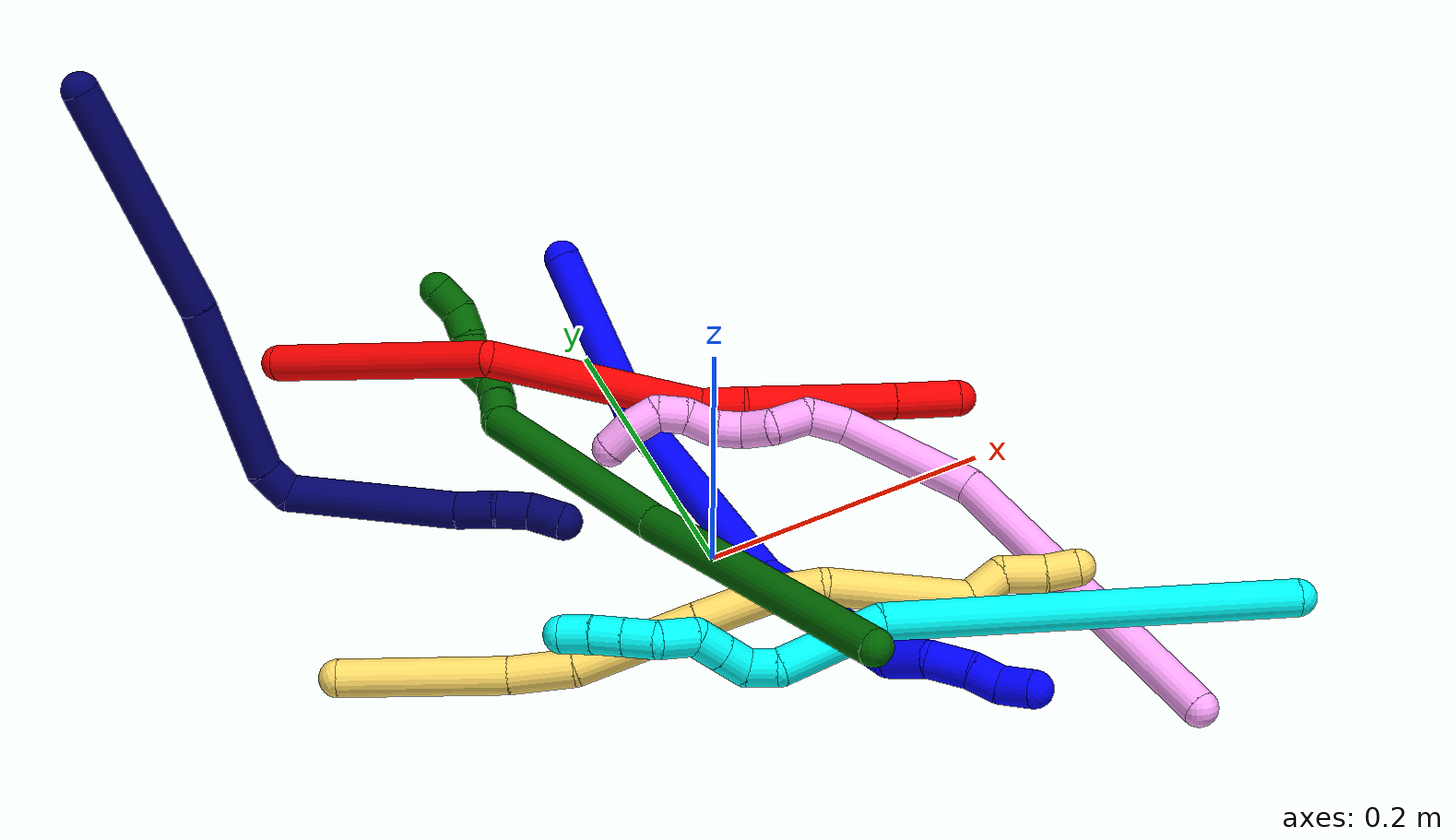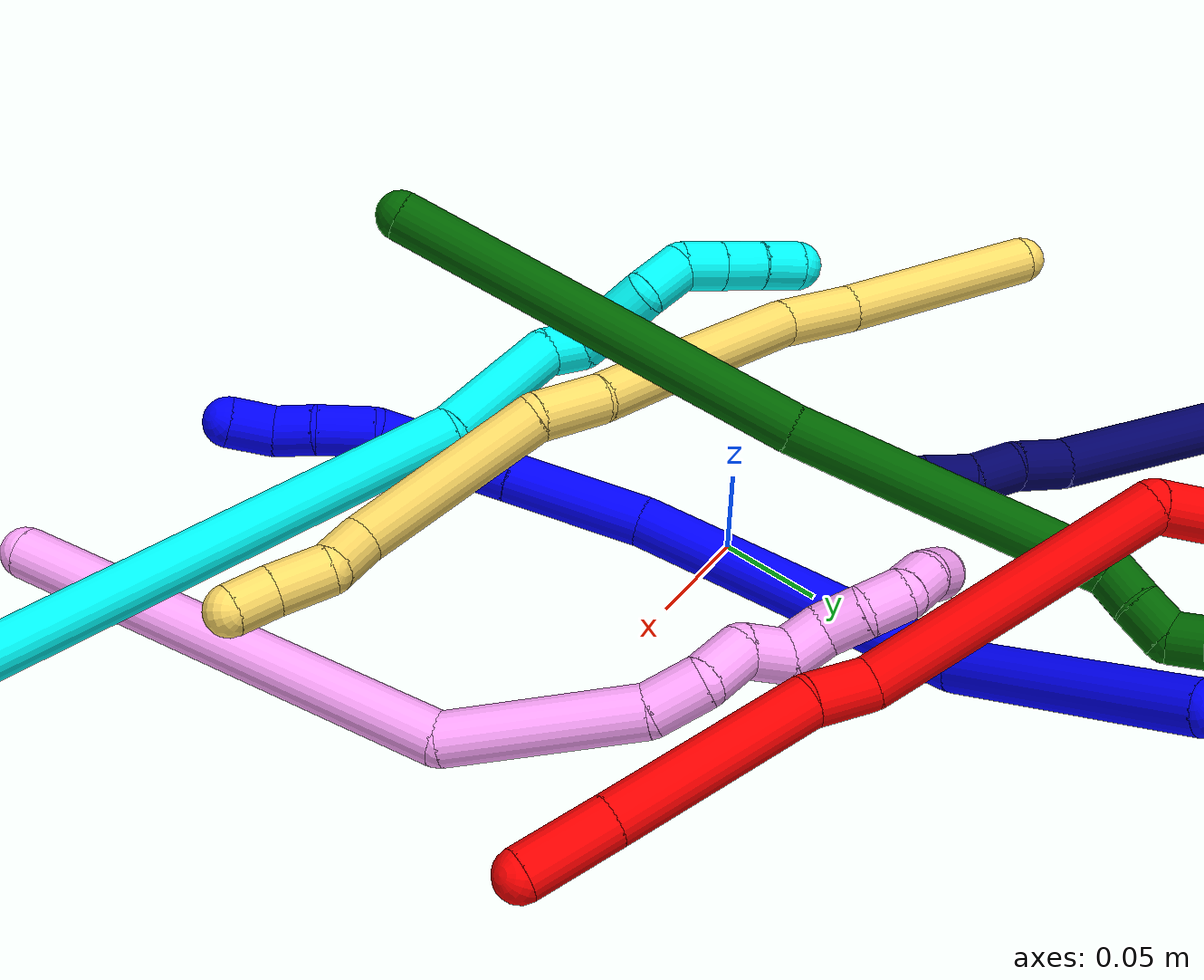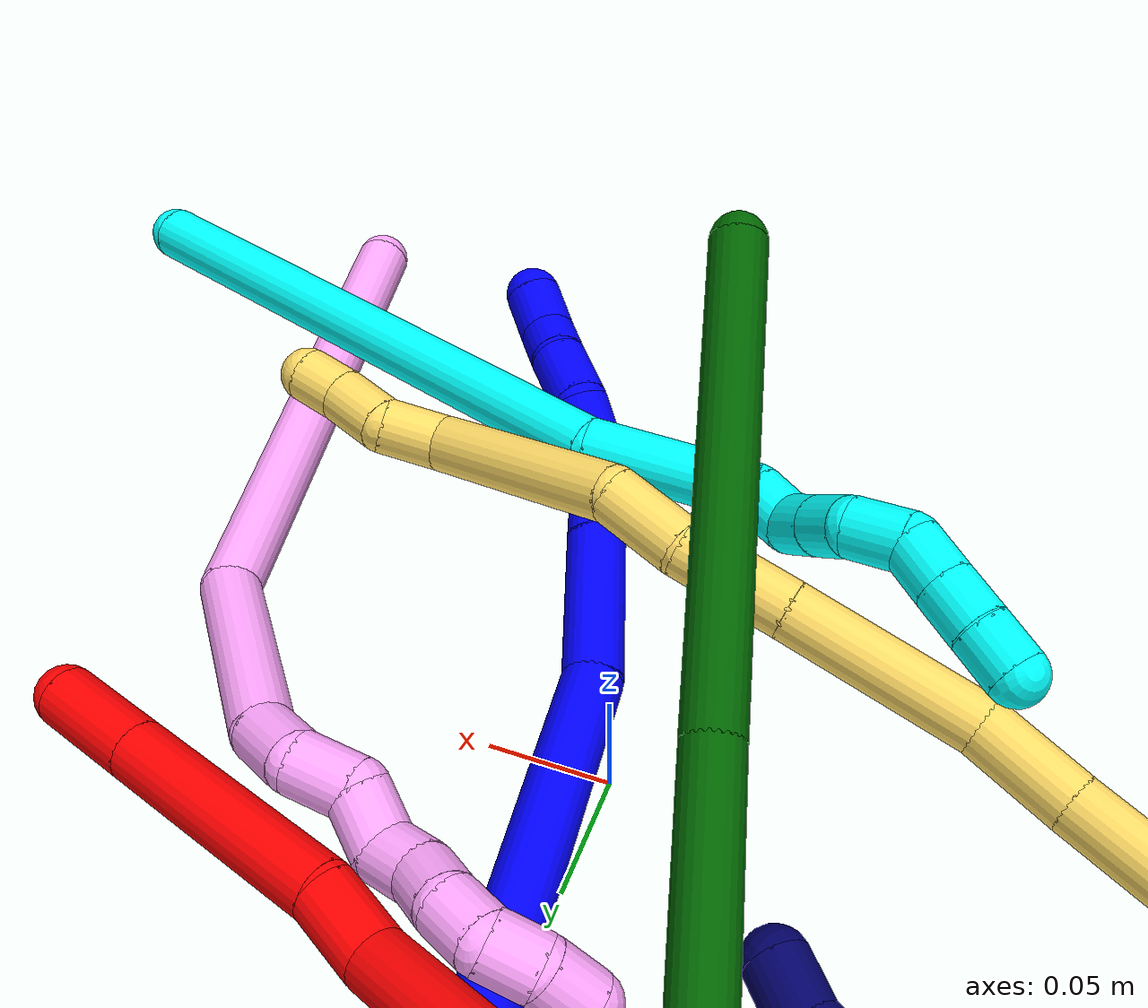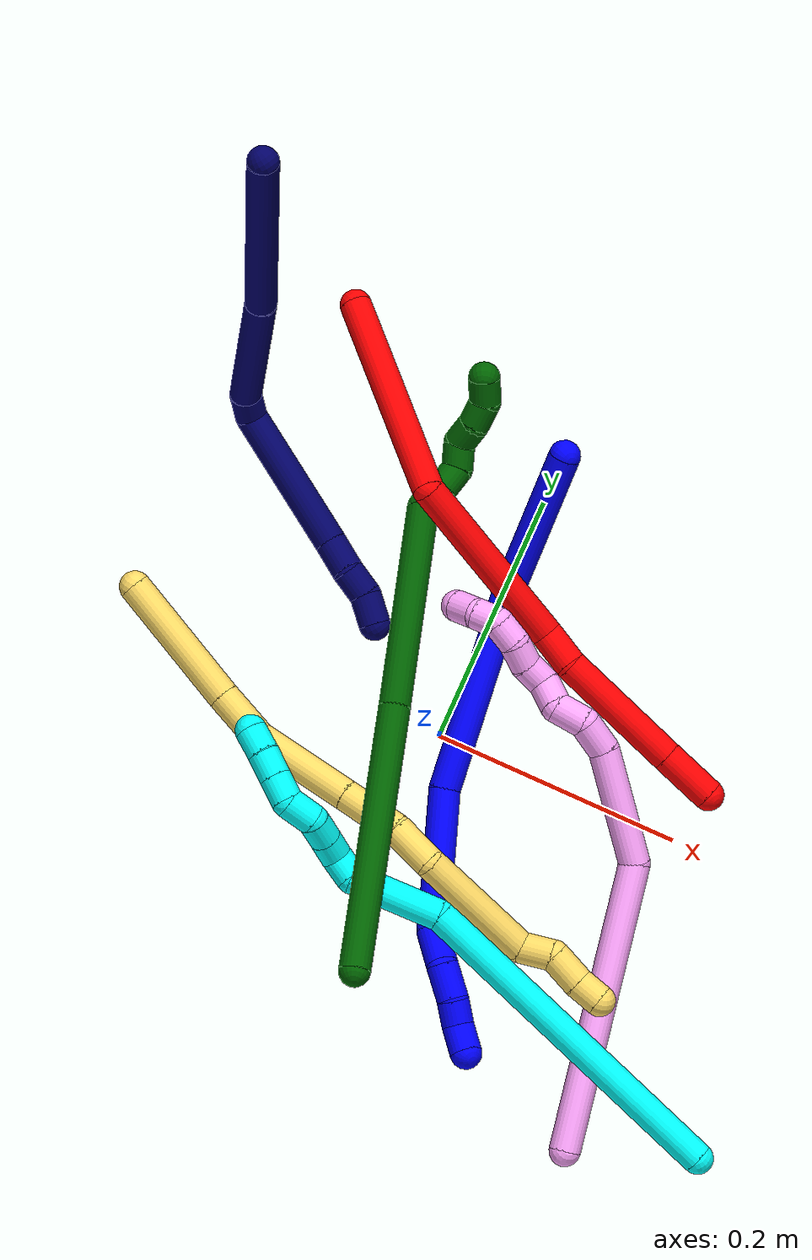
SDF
<sdf version="1.7">
 <world name="default">
  <plugin name="TubeGeneratorPlugin" filename="libtube_generator_plugin.so"/>
  <model name="photoneo_s_sensor">
   <static>1</static>
   <pose>0 0 2 1.57079 1.57079 3.14159</pose>
   <link name="link">
    <inertial><mass>0.1</mass></inertial>
    <sensor name="sensor" type="depth">
     <update_rate>30</update_rate>
     <camera>
      <horizontal_fov>1.22</horizontal_fov>
      <image><width>1920</width><height>1200</height><format>B8G8R8</format></image>
      <clip><near>0.1</near><far>4</far></clip>
      <depth_camera><output>points</output></depth_camera>
     </camera>
     <plugin name="camera_plugin" filename="libgazebo_ros_depth_camera.so">
      <baseline>0.2</baseline>
      <alwaysOn>1</alwaysOn>
      <updateRate>0.0</updateRate>
      <cameraName>camera_ir</cameraName>
      <imageTopicName>/camera/color/image_raw</imageTopicName>
      <cameraInfoTopicName>/camera/color/camera_info</cameraInfoTopicName>
      <depthImageTopicName>/camera/depth/image_raw</depthImageTopicName>
      <depthImageCameraInfoTopicName>/camera/depth/camera_info</depthImageCameraInfoTopicName>
      <pointCloudTopicName>/camera/depth/points</pointCloudTopicName>
      <frameName>fr_optical</frameName>
      <pointCloudCutoff>0.1</pointCloudCutoff>
      <pointCloudCutoffMax>2.0</pointCloudCutoffMax>
      <distortionK1>0</distortionK1>
      <distortionK2>0</distortionK2>
      <distortionK3>0</distortionK3>
      <distortionT1>0</distortionT1>
      <distortionT2>0</distortionT2>
      <CxPrime>0</CxPrime>
      <Cx>0</Cx>
      <Cy>0</Cy>
      <focalLength>0</focalLength>
      <hackBaseline>0</hackBaseline>
     </plugin>
    </sensor>
   </link>
  </model>
  <gravity>0 0 -9.8</gravity>
  <magnetic_field>6e-06 2.3e-05 -4.2e-05</magnetic_field>
  <atmosphere type="adiabatic"/>
  <physics name="default_physics" default="0" type="ode">
   <max_step_size>0.003</max_step_size>
   <real_time_factor>1</real_time_factor>
   <real_time_update_rate>1000</real_time_update_rate>
   <max_contacts>10000</max_contacts>
   <ode>
    <solver>
     <type>quick</type>
     <iters>100</iters>
     <sor>1.3</sor>
     <use_dynamic_moi_rescaling>0</use_dynamic_moi_rescaling>
    </solver>
    <constraints>
     <contact_max_correcting_vel>0</contact_max_correcting_vel>
     <contact_surface_layer>0.001</contact_surface_layer>
     <cfm>0</cfm>
     <erp>0.2</erp>
    </constraints>
   </ode>
  </physics>
  <scene><ambient>0.4 0.4 0.4 1</ambient><background>0.7 0.7 0.7 1</background><shadows>0</shadows></scene>
  <audio><device>default</device></audio>
  <spherical_coordinates>
   <surface_model>EARTH_WGS84</surface_model>
   <latitude_deg>0</latitude_deg>
   <longitude_deg>0</longitude_deg>
   <elevation>0</elevation>
   <heading_deg>0</heading_deg>
  </spherical_coordinates>
  <model name="bin">
   <static>1</static>
   <link name="bottom">
    <collision name="collision-bottom">
     <pose>0 0 -0.01 0 -0 0</pose>
     <geometry><box><size>0.8 0.6 0.02</size></box></geometry>
     <surface>
      <friction><ode><mu>100</mu><mu2>100</mu2></ode></friction>
      <contact><collide_bitmask>65535</collide_bitmask></contact>
     </surface>
    </collision>
   </link>
   <link name="west_wall">
    <collision name="collision-west_wall">
     <pose>-0.41 0 0.1 0 -0 0</pose>
     <geometry><box><size>0.02 0.6 0.2</size></box></geometry>
     <surface>
      <friction><ode><mu>100</mu><mu2>100</mu2></ode></friction>
      <contact><collide_bitmask>65535</collide_bitmask></contact>
     </surface>
    </collision>
   </link>
   <link name="east_wall">
    <collision name="collision-east_wall">
     <pose>0.41 0 0.1 0 -0 0</pose>
     <geometry><box><size>0.02 0.6 0.2</size></box></geometry>
     <surface>
      <friction><ode><mu>100</mu><mu2>100</mu2></ode></friction>
      <contact><collide_bitmask>65535</collide_bitmask></contact>
     </surface>
    </collision>
   </link>
   <link name="south_wall">
    <collision name="collision-south_wall">
     <pose>0 -0.31 0.1 0 -0 0</pose>
     <geometry><box><size>0.8 0.02 0.2</size></box></geometry>
     <surface>
      <friction><ode><mu>100</mu><mu2>100</mu2></ode></friction>
      <contact><collide_bitmask>65535</collide_bitmask></contact>
     </surface>
    </collision>
   </link>
   <link name="north_wall">
    <collision name="collision-north_wall">
     <pose>0 0.31 0.1 0 -0 0</pose>
     <geometry><box><size>0.8 0.02 0.2</size></box></geometry>
     <surface>
      <friction><ode><mu>100</mu><mu2>100</mu2></ode></friction>
      <contact><collide_bitmask>65535</collide_bitmask></contact>
     </surface>
    </collision>
   </link>
  </model>
  <model name="1">
   <static>0</static>
   <link name="1">
    <collision name="collision-cylinder-e_1_1_4">
     <pose>-0.017609 -0.057924 0.006851 1.45307 -0.2932 -0.260957</pose>
     <geometry><cylinder><radius>0.0125</radius><length>0.121856</length></cylinder></geometry>
     <surface>
      <friction><ode><mu>1.16</mu><mu2>1.16</mu2><slip1>0</slip1><slip2>0</slip2></ode></friction>
      <contact><ode><kp>1e+06</kp><kd>1</kd><max_vel>0</max_vel><min_depth>0.001</min_depth></ode></contact>
     </surface>
    </collision>
    <visual name="visual-cylinder-e_1_1_4">
     <pose>-0.017609 -0.057924 0.006851 1.45307 -0.2932 -0.260957</pose>
     <geometry><cylinder><radius>0.0125</radius><length>0.121856</length></cylinder></geometry>
     <material><ambient>0 0 1 1</ambient></material>
    </visual>
    <collision name="collision-cylinder-e_2_4_5">
     <pose>-0.041423 -0.193742 -0.01206 1.89021 -0.075479 -0.104418</pose>
     <geometry><cylinder><radius>0.0125</radius><length>0.164555</length></cylinder></geometry>
     <surface>
      <friction><ode><mu>1.16</mu><mu2>1.16</mu2><slip1>0</slip1><slip2>0</slip2></ode></friction>
      <contact><ode><kp>1e+06</kp><kd>1</kd><max_vel>0</max_vel><min_depth>0.001</min_depth></ode></contact>
     </surface>
    </collision>
    <visual name="visual-cylinder-e_2_4_5">
     <pose>-0.041423 -0.193742 -0.01206 1.89021 -0.075479 -0.104418</pose>
     <geometry><cylinder><radius>0.0125</radius><length>0.164555</length></cylinder></geometry>
     <material><ambient>0 0 1 1</ambient></material>
    </visual>
    <collision name="collision-cylinder-e_3_5_6">
     <pose>-0.053959 -0.300524 -0.055786 2.12709 -0.184014 -0.329042</pose>
     <geometry><cylinder><radius>0.0125</radius><length>0.069204</length></cylinder></geometry>
     <surface>
      <friction><ode><mu>1.16</mu><mu2>1.16</mu2><slip1>0</slip1><slip2>0</slip2></ode></friction>
      <contact><ode><kp>1e+06</kp><kd>1</kd><max_vel>0</max_vel><min_depth>0.001</min_depth></ode></contact>
     </surface>
    </collision>
    <visual name="visual-cylinder-e_3_5_6">
     <pose>-0.053959 -0.300524 -0.055786 2.12709 -0.184014 -0.329042</pose>
     <geometry><cylinder><radius>0.0125</radius><length>0.069204</length></cylinder></geometry>
     <material><ambient>0 0 1 1</ambient></material>
    </visual>
    <collision name="collision-cylinder-e_4_6_7">
     <pose>-0.064103 -0.347033 -0.083996 2.09756 -0.184931 -0.319652</pose>
     <geometry><cylinder><radius>0.0125</radius><length>0.041474</length></cylinder></geometry>
     <surface>
      <friction><ode><mu>1.16</mu><mu2>1.16</mu2><slip1>0</slip1><slip2>0</slip2></ode></friction>
      <contact><ode><kp>1e+06</kp><kd>1</kd><max_vel>0</max_vel><min_depth>0.001</min_depth></ode></contact>
     </surface>
    </collision>
    <visual name="visual-cylinder-e_4_6_7">
     <pose>-0.064103 -0.347033 -0.083996 2.09756 -0.184931 -0.319652</pose>
     <geometry><cylinder><radius>0.0125</radius><length>0.041474</length></cylinder></geometry>
     <material><ambient>0 0 1 1</ambient></material>
    </visual>
    <collision name="collision-cylinder-e_5_7_8">
     <pose>-0.070366 -0.371959 -0.10748 2.63724 -0.16064 -0.605591</pose>
     <geometry><cylinder><radius>0.0125</radius><length>0.030633</length></cylinder></geometry>
     <surface>
      <friction><ode><mu>1.16</mu><mu2>1.16</mu2><slip1>0</slip1><slip2>0</slip2></ode></friction>
      <contact><ode><kp>1e+06</kp><kd>1</kd><max_vel>0</max_vel><min_depth>0.001</min_depth></ode></contact>
     </surface>
    </collision>
    <visual name="visual-cylinder-e_5_7_8">
     <pose>-0.070366 -0.371959 -0.10748 2.63724 -0.16064 -0.605591</pose>
     <geometry><cylinder><radius>0.0125</radius><length>0.030633</length></cylinder></geometry>
     <material><ambient>0 0 1 1</ambient></material>
    </visual>
    <collision name="collision-cylinder-e_6_8_9">
     <pose>-0.079176 -0.387955 -0.130056 2.39224 -0.46254 -1.07909</pose>
     <geometry><cylinder><radius>0.0125</radius><length>0.028508</length></cylinder></geometry>
     <surface>
      <friction><ode><mu>1.16</mu><mu2>1.16</mu2><slip1>0</slip1><slip2>0</slip2></ode></friction>
      <contact><ode><kp>1e+06</kp><kd>1</kd><max_vel>0</max_vel><min_depth>0.001</min_depth></ode></contact>
     </surface>
    </collision>
    <visual name="visual-cylinder-e_6_8_9">
     <pose>-0.079176 -0.387955 -0.130056 2.39224 -0.46254 -1.07909</pose>
     <geometry><cylinder><radius>0.0125</radius><length>0.028508</length></cylinder></geometry>
     <material><ambient>0 0 1 1</ambient></material>
    </visual>
    <collision name="collision-cylinder-e_7_9_10">
     <pose>-0.090798 -0.404099 -0.144248 2.14779 -0.534051 -0.93441</pose>
     <geometry><cylinder><radius>0.0125</radius><length>0.020669</length></cylinder></geometry>
     <surface>
      <friction><ode><mu>1.16</mu><mu2>1.16</mu2><slip1>0</slip1><slip2>0</slip2></ode></friction>
      <contact><ode><kp>1e+06</kp><kd>1</kd><max_vel>0</max_vel><min_depth>0.001</min_depth></ode></contact>
     </surface>
    </collision>
    <visual name="visual-cylinder-e_7_9_10">
     <pose>-0.090798 -0.404099 -0.144248 2.14779 -0.534051 -0.93441</pose>
     <geometry><cylinder><radius>0.0125</radius><length>0.020669</length></cylinder></geometry>
     <material><ambient>0 0 1 1</ambient></material>
    </visual>
    <collision name="collision-cylinder-e_8_10_2">
     <pose>-0.099364 -0.417873 -0.158186 2.53393 -0.290325 -0.872583</pose>
     <geometry><cylinder><radius>0.0125</radius><length>0.0231</length></cylinder></geometry>
     <surface>
      <friction><ode><mu>1.16</mu><mu2>1.16</mu2><slip1>0</slip1><slip2>0</slip2></ode></friction>
      <contact><ode><kp>1e+06</kp><kd>1</kd><max_vel>0</max_vel><min_depth>0.001</min_depth></ode></contact>
     </surface>
    </collision>
    <visual name="visual-cylinder-e_8_10_2">
     <pose>-0.099364 -0.417873 -0.158186 2.53393 -0.290325 -0.872583</pose>
     <geometry><cylinder><radius>0.0125</radius><length>0.0231</length></cylinder></geometry>
     <material><ambient>0 0 1 1</ambient></material>
    </visual>
    <collision name="collision-sphere-2">
     <pose>-0.102671 -0.424192 -0.167272 0 -0 0</pose>
     <geometry><sphere><radius>0.0125</radius></sphere></geometry>
     <surface>
      <friction><ode><mu>1.16</mu><mu2>1.16</mu2><slip1>0</slip1><slip2>0</slip2></ode></friction>
      <contact><ode><kp>1e+06</kp><kd>1</kd><max_vel>0</max_vel><min_depth>0.001</min_depth></ode></contact>
     </surface>
    </collision>
    <visual name="visual-sphere-2">
     <pose>-0.102671 -0.424192 -0.167272 0 -0 0</pose>
     <geometry><sphere><radius>0.0125</radius></sphere></geometry>
     <material><ambient>0 0 1 1</ambient></material>
    </visual>
    <collision name="collision-sphere-10">
     <pose>-0.096058 -0.411555 -0.149101 0 -0 0</pose>
     <geometry><sphere><radius>0.0125</radius></sphere></geometry>
     <surface>
      <friction><ode><mu>1.16</mu><mu2>1.16</mu2><slip1>0</slip1><slip2>0</slip2></ode></friction>
      <contact><ode><kp>1e+06</kp><kd>1</kd><max_vel>0</max_vel><min_depth>0.001</min_depth></ode></contact>
     </surface>
    </collision>
    <visual name="visual-sphere-10">
     <pose>-0.096058 -0.411555 -0.149101 0 -0 0</pose>
     <geometry><sphere><radius>0.0125</radius></sphere></geometry>
     <material><ambient>0 0 1 1</ambient></material>
    </visual>
    <collision name="collision-sphere-9">
     <pose>-0.085537 -0.396644 -0.139396 0 -0 0</pose>
     <geometry><sphere><radius>0.0125</radius></sphere></geometry>
     <surface>
      <friction><ode><mu>1.16</mu><mu2>1.16</mu2><slip1>0</slip1><slip2>0</slip2></ode></friction>
      <contact><ode><kp>1e+06</kp><kd>1</kd><max_vel>0</max_vel><min_depth>0.001</min_depth></ode></contact>
     </surface>
    </collision>
    <visual name="visual-sphere-9">
     <pose>-0.085537 -0.396644 -0.139396 0 -0 0</pose>
     <geometry><sphere><radius>0.0125</radius></sphere></geometry>
     <material><ambient>0 0 1 1</ambient></material>
    </visual>
    <collision name="collision-sphere-4">
     <pose>-0.035219 -0.115849 0.013702 0 -0 0</pose>
     <geometry><sphere><radius>0.0125</radius></sphere></geometry>
     <surface>
      <friction><ode><mu>1.16</mu><mu2>1.16</mu2><slip1>0</slip1><slip2>0</slip2></ode></friction>
      <contact><ode><kp>1e+06</kp><kd>1</kd><max_vel>0</max_vel><min_depth>0.001</min_depth></ode></contact>
     </surface>
    </collision>
    <visual name="visual-sphere-4">
     <pose>-0.035219 -0.115849 0.013702 0 -0 0</pose>
     <geometry><sphere><radius>0.0125</radius></sphere></geometry>
     <material><ambient>0 0 1 1</ambient></material>
    </visual>
    <collision name="collision-sphere-1">
     <geometry><sphere><radius>0.0125</radius></sphere></geometry>
     <surface>
      <friction><ode><mu>1.16</mu><mu2>1.16</mu2><slip1>0</slip1><slip2>0</slip2></ode></friction>
      <contact><ode><kp>1e+06</kp><kd>1</kd><max_vel>0</max_vel><min_depth>0.001</min_depth></ode></contact>
     </surface>
    </collision>
    <visual name="visual-sphere-1">
     <geometry><sphere><radius>0.0125</radius></sphere></geometry>
     <material><ambient>0 0 1 1</ambient></material>
    </visual>
    <collision name="collision-sphere-8">
     <pose>-0.072816 -0.379266 -0.120717 0 -0 0</pose>
     <geometry><sphere><radius>0.0125</radius></sphere></geometry>
     <surface>
      <friction><ode><mu>1.16</mu><mu2>1.16</mu2><slip1>0</slip1><slip2>0</slip2></ode></friction>
      <contact><ode><kp>1e+06</kp><kd>1</kd><max_vel>0</max_vel><min_depth>0.001</min_depth></ode></contact>
     </surface>
    </collision>
    <visual name="visual-sphere-8">
     <pose>-0.072816 -0.379266 -0.120717 0 -0 0</pose>
     <geometry><sphere><radius>0.0125</radius></sphere></geometry>
     <material><ambient>0 0 1 1</ambient></material>
    </visual>
    <collision name="collision-sphere-5">
     <pose>-0.047627 -0.271635 -0.037823 0 -0 0</pose>
     <geometry><sphere><radius>0.0125</radius></sphere></geometry>
     <surface>
      <friction><ode><mu>1.16</mu><mu2>1.16</mu2><slip1>0</slip1><slip2>0</slip2></ode></friction>
      <contact><ode><kp>1e+06</kp><kd>1</kd><max_vel>0</max_vel><min_depth>0.001</min_depth></ode></contact>
     </surface>
    </collision>
    <visual name="visual-sphere-5">
     <pose>-0.047627 -0.271635 -0.037823 0 -0 0</pose>
     <geometry><sphere><radius>0.0125</radius></sphere></geometry>
     <material><ambient>0 0 1 1</ambient></material>
    </visual>
    <collision name="collision-sphere-6">
     <pose>-0.06029 -0.329413 -0.073749 0 -0 0</pose>
     <geometry><sphere><radius>0.0125</radius></sphere></geometry>
     <surface>
      <friction><ode><mu>1.16</mu><mu2>1.16</mu2><slip1>0</slip1><slip2>0</slip2></ode></friction>
      <contact><ode><kp>1e+06</kp><kd>1</kd><max_vel>0</max_vel><min_depth>0.001</min_depth></ode></contact>
     </surface>
    </collision>
    <visual name="visual-sphere-6">
     <pose>-0.06029 -0.329413 -0.073749 0 -0 0</pose>
     <geometry><sphere><radius>0.0125</radius></sphere></geometry>
     <material><ambient>0 0 1 1</ambient></material>
    </visual>
    <collision name="collision-sphere-7">
     <pose>-0.067916 -0.364653 -0.094243 0 -0 0</pose>
     <geometry><sphere><radius>0.0125</radius></sphere></geometry>
     <surface>
      <friction><ode><mu>1.16</mu><mu2>1.16</mu2><slip1>0</slip1><slip2>0</slip2></ode></friction>
      <contact><ode><kp>1e+06</kp><kd>1</kd><max_vel>0</max_vel><min_depth>0.001</min_depth></ode></contact>
     </surface>
    </collision>
    <visual name="visual-sphere-7">
     <pose>-0.067916 -0.364653 -0.094243 0 -0 0</pose>
     <geometry><sphere><radius>0.0125</radius></sphere></geometry>
     <material><ambient>0 0 1 1</ambient></material>
    </visual>
    <inertial>
     <pose>-0.047879 -0.229179 -0.044259 0 -0 0</pose>
     <mass>0.5</mass>
     <inertia>
      <ixx>0.000455</ixx>
      <ixy>0</ixy>
      <ixz>0</ixz>
      <iyy>-0.000236</iyy>
      <iyz>0</iyz>
      <izz>0.000614</izz>
     </inertia>
    </inertial>
   </link>
   <pose>0.000387 0.235698 0.068113 2.87652 -0.6621 -3.12692</pose>
  </model>
  <model name="2">
   <static>0</static>
   <link name="2">
    <collision name="collision-cylinder-e_1_1_4">
     <pose>0.037938 -0.009777 -0.075334 3.01254 0.463181 2.6067</pose>
     <geometry><cylinder><radius>0.0125</radius><length>0.169824</length></cylinder></geometry>
     <surface>
      <friction><ode><mu>1.16</mu><mu2>1.16</mu2><slip1>0</slip1><slip2>0</slip2></ode></friction>
      <contact><ode><kp>1e+06</kp><kd>1</kd><max_vel>0</max_vel><min_depth>0.001</min_depth></ode></contact>
     </surface>
    </collision>
    <visual name="visual-cylinder-e_1_1_4">
     <pose>0.037938 -0.009777 -0.075334 3.01254 0.463181 2.6067</pose>
     <geometry><cylinder><radius>0.0125</radius><length>0.169824</length></cylinder></geometry>
     <material><ambient>1 0 0 1</ambient></material>
    </visual>
    <collision name="collision-cylinder-e_2_4_5">
     <pose>0.100547 -0.077961 -0.19146 2.18046 0.333364 0.624335</pose>
     <geometry><cylinder><radius>0.0125</radius><length>0.150786</length></cylinder></geometry>
     <surface>
      <friction><ode><mu>1.16</mu><mu2>1.16</mu2><slip1>0</slip1><slip2>0</slip2></ode></friction>
      <contact><ode><kp>1e+06</kp><kd>1</kd><max_vel>0</max_vel><min_depth>0.001</min_depth></ode></contact>
     </surface>
    </collision>
    <visual name="visual-cylinder-e_2_4_5">
     <pose>0.100547 -0.077961 -0.19146 2.18046 0.333364 0.624335</pose>
     <geometry><cylinder><radius>0.0125</radius><length>0.150786</length></cylinder></geometry>
     <material><ambient>1 0 0 1</ambient></material>
    </visual>
    <collision name="collision-cylinder-e_3_5_6">
     <pose>0.129725 -0.143504 -0.245373 2.64345 0.293117 1.05172</pose>
     <geometry><cylinder><radius>0.0125</radius><length>0.031201</length></cylinder></geometry>
     <surface>
      <friction><ode><mu>1.16</mu><mu2>1.16</mu2><slip1>0</slip1><slip2>0</slip2></ode></friction>
      <contact><ode><kp>1e+06</kp><kd>1</kd><max_vel>0</max_vel><min_depth>0.001</min_depth></ode></contact>
     </surface>
    </collision>
    <visual name="visual-cylinder-e_3_5_6">
     <pose>0.129725 -0.143504 -0.245373 2.64345 0.293117 1.05172</pose>
     <geometry><cylinder><radius>0.0125</radius><length>0.031201</length></cylinder></geometry>
     <material><ambient>1 0 0 1</ambient></material>
    </visual>
    <collision name="collision-cylinder-e_4_6_7">
     <pose>0.143646 -0.184992 -0.295853 2.39811 0.18339 0.463247</pose>
     <geometry><cylinder><radius>0.0125</radius><length>0.103236</length></cylinder></geometry>
     <surface>
      <friction><ode><mu>1.16</mu><mu2>1.16</mu2><slip1>0</slip1><slip2>0</slip2></ode></friction>
      <contact><ode><kp>1e+06</kp><kd>1</kd><max_vel>0</max_vel><min_depth>0.001</min_depth></ode></contact>
     </surface>
    </collision>
    <visual name="visual-cylinder-e_4_6_7">
     <pose>0.143646 -0.184992 -0.295853 2.39811 0.18339 0.463247</pose>
     <geometry><cylinder><radius>0.0125</radius><length>0.103236</length></cylinder></geometry>
     <material><ambient>1 0 0 1</ambient></material>
    </visual>
    <collision name="collision-cylinder-e_5_7_2">
     <pose>0.156881 -0.233932 -0.349879 2.42256 0.170854 0.448041</pose>
     <geometry><cylinder><radius>0.0125</radius><length>0.044953</length></cylinder></geometry>
     <surface>
      <friction><ode><mu>1.16</mu><mu2>1.16</mu2><slip1>0</slip1><slip2>0</slip2></ode></friction>
      <contact><ode><kp>1e+06</kp><kd>1</kd><max_vel>0</max_vel><min_depth>0.001</min_depth></ode></contact>
     </surface>
    </collision>
    <visual name="visual-cylinder-e_5_7_2">
     <pose>0.156881 -0.233932 -0.349879 2.42256 0.170854 0.448041</pose>
     <geometry><cylinder><radius>0.0125</radius><length>0.044953</length></cylinder></geometry>
     <material><ambient>1 0 0 1</ambient></material>
    </visual>
    <collision name="collision-sphere-2">
     <pose>0.160702 -0.248521 -0.366545 0 -0 0</pose>
     <geometry><sphere><radius>0.0125</radius></sphere></geometry>
     <surface>
      <friction><ode><mu>1.16</mu><mu2>1.16</mu2><slip1>0</slip1><slip2>0</slip2></ode></friction>
      <contact><ode><kp>1e+06</kp><kd>1</kd><max_vel>0</max_vel><min_depth>0.001</min_depth></ode></contact>
     </surface>
    </collision>
    <visual name="visual-sphere-2">
     <pose>0.160702 -0.248521 -0.366545 0 -0 0</pose>
     <geometry><sphere><radius>0.0125</radius></sphere></geometry>
     <material><ambient>1 0 0 1</ambient></material>
    </visual>
    <collision name="collision-sphere-7">
     <pose>0.153059 -0.219344 -0.333213 0 -0 0</pose>
     <geometry><sphere><radius>0.0125</radius></sphere></geometry>
     <surface>
      <friction><ode><mu>1.16</mu><mu2>1.16</mu2><slip1>0</slip1><slip2>0</slip2></ode></friction>
      <contact><ode><kp>1e+06</kp><kd>1</kd><max_vel>0</max_vel><min_depth>0.001</min_depth></ode></contact>
     </surface>
    </collision>
    <visual name="visual-sphere-7">
     <pose>0.153059 -0.219344 -0.333213 0 -0 0</pose>
     <geometry><sphere><radius>0.0125</radius></sphere></geometry>
     <material><ambient>1 0 0 1</ambient></material>
    </visual>
    <collision name="collision-sphere-6">
     <pose>0.134233 -0.15064 -0.258494 0 -0 0</pose>
     <geometry><sphere><radius>0.0125</radius></sphere></geometry>
     <surface>
      <friction><ode><mu>1.16</mu><mu2>1.16</mu2><slip1>0</slip1><slip2>0</slip2></ode></friction>
      <contact><ode><kp>1e+06</kp><kd>1</kd><max_vel>0</max_vel><min_depth>0.001</min_depth></ode></contact>
     </surface>
    </collision>
    <visual name="visual-sphere-6">
     <pose>0.134233 -0.15064 -0.258494 0 -0 0</pose>
     <geometry><sphere><radius>0.0125</radius></sphere></geometry>
     <material><ambient>1 0 0 1</ambient></material>
    </visual>
    <collision name="collision-sphere-5">
     <pose>0.125218 -0.136368 -0.232253 0 -0 0</pose>
     <geometry><sphere><radius>0.0125</radius></sphere></geometry>
     <surface>
      <friction><ode><mu>1.16</mu><mu2>1.16</mu2><slip1>0</slip1><slip2>0</slip2></ode></friction>
      <contact><ode><kp>1e+06</kp><kd>1</kd><max_vel>0</max_vel><min_depth>0.001</min_depth></ode></contact>
     </surface>
    </collision>
    <visual name="visual-sphere-5">
     <pose>0.125218 -0.136368 -0.232253 0 -0 0</pose>
     <geometry><sphere><radius>0.0125</radius></sphere></geometry>
     <material><ambient>1 0 0 1</ambient></material>
    </visual>
    <collision name="collision-sphere-1">
     <geometry><sphere><radius>0.0125</radius></sphere></geometry>
     <surface>
      <friction><ode><mu>1.16</mu><mu2>1.16</mu2><slip1>0</slip1><slip2>0</slip2></ode></friction>
      <contact><ode><kp>1e+06</kp><kd>1</kd><max_vel>0</max_vel><min_depth>0.001</min_depth></ode></contact>
     </surface>
    </collision>
    <visual name="visual-sphere-1">
     <geometry><sphere><radius>0.0125</radius></sphere></geometry>
     <material><ambient>1 0 0 1</ambient></material>
    </visual>
    <collision name="collision-sphere-4">
     <pose>0.075877 -0.019553 -0.150667 0 -0 0</pose>
     <geometry><sphere><radius>0.0125</radius></sphere></geometry>
     <surface>
      <friction><ode><mu>1.16</mu><mu2>1.16</mu2><slip1>0</slip1><slip2>0</slip2></ode></friction>
      <contact><ode><kp>1e+06</kp><kd>1</kd><max_vel>0</max_vel><min_depth>0.001</min_depth></ode></contact>
     </surface>
    </collision>
    <visual name="visual-sphere-4">
     <pose>0.075877 -0.019553 -0.150667 0 -0 0</pose>
     <geometry><sphere><radius>0.0125</radius></sphere></geometry>
     <material><ambient>1 0 0 1</ambient></material>
    </visual>
    <inertial>
     <pose>0.095066 -0.095014 -0.191179 0 -0 0</pose>
     <mass>0.5</mass>
     <inertia><ixx>0.00041</ixx><ixy>0</ixy><ixz>0</ixz><iyy>0.000591</iyy><iyz>0</iyz><izz>1.6e-05</izz></inertia>
    </inertial>
   </link>
   <pose>-0.196965 0.280832 0.011723 2.2508 0.223052 -1.74065</pose>
  </model>
  <model name="3">
   <static>0</static>
   <link name="3">
    <collision name="collision-cylinder-e_1_1_4">
     <pose>-0.076578 0.07604 -0.08519 -2.41288 -0.590733 1.34679</pose>
     <geometry><cylinder><radius>0.0125</radius><length>0.27498</length></cylinder></geometry>
     <surface>
      <friction><ode><mu>1.16</mu><mu2>1.16</mu2><slip1>0</slip1><slip2>0</slip2></ode></friction>
      <contact><ode><kp>1e+06</kp><kd>1</kd><max_vel>0</max_vel><min_depth>0.001</min_depth></ode></contact>
     </surface>
    </collision>
    <visual name="visual-cylinder-e_1_1_4">
     <pose>-0.076578 0.07604 -0.08519 -2.41288 -0.590733 1.34679</pose>
     <geometry><cylinder><radius>0.0125</radius><length>0.27498</length></cylinder></geometry>
     <material><ambient>0.003922 1 0.996078 1</ambient></material>
    </visual>
    <collision name="collision-cylinder-e_2_4_5">
     <pose>-0.167015 0.182428 -0.186576 -2.06104 -0.382999 0.625258</pose>
     <geometry><cylinder><radius>0.0125</radius><length>0.074173</length></cylinder></geometry>
     <surface>
      <friction><ode><mu>1.16</mu><mu2>1.16</mu2><slip1>0</slip1><slip2>0</slip2></ode></friction>
      <contact><ode><kp>1e+06</kp><kd>1</kd><max_vel>0</max_vel><min_depth>0.001</min_depth></ode></contact>
     </surface>
    </collision>
    <visual name="visual-cylinder-e_2_4_5">
     <pose>-0.167015 0.182428 -0.186576 -2.06104 -0.382999 0.625258</pose>
     <geometry><cylinder><radius>0.0125</radius><length>0.074173</length></cylinder></geometry>
     <material><ambient>0.003922 1 0.996078 1</ambient></material>
    </visual>
    <collision name="collision-cylinder-e_3_5_6">
     <pose>-0.188558 0.217229 -0.208081 -2.44352 -0.837008 1.77007</pose>
     <geometry><cylinder><radius>0.0125</radius><length>0.020694</length></cylinder></geometry>
     <surface>
      <friction><ode><mu>1.16</mu><mu2>1.16</mu2><slip1>0</slip1><slip2>0</slip2></ode></friction>
      <contact><ode><kp>1e+06</kp><kd>1</kd><max_vel>0</max_vel><min_depth>0.001</min_depth></ode></contact>
     </surface>
    </collision>
    <visual name="visual-cylinder-e_3_5_6">
     <pose>-0.188558 0.217229 -0.208081 -2.44352 -0.837008 1.77007</pose>
     <geometry><cylinder><radius>0.0125</radius><length>0.020694</length></cylinder></geometry>
     <material><ambient>0.003922 1 0.996078 1</ambient></material>
    </visual>
    <collision name="collision-cylinder-e_4_6_7">
     <pose>-0.198718 0.222928 -0.223744 -3.02193 -0.233095 2.19572</pose>
     <geometry><cylinder><radius>0.0125</radius><length>0.021438</length></cylinder></geometry>
     <surface>
      <friction><ode><mu>1.16</mu><mu2>1.16</mu2><slip1>0</slip1><slip2>0</slip2></ode></friction>
      <contact><ode><kp>1e+06</kp><kd>1</kd><max_vel>0</max_vel><min_depth>0.001</min_depth></ode></contact>
     </surface>
    </collision>
    <visual name="visual-cylinder-e_4_6_7">
     <pose>-0.198718 0.222928 -0.223744 -3.02193 -0.233095 2.19572</pose>
     <geometry><cylinder><radius>0.0125</radius><length>0.021438</length></cylinder></geometry>
     <material><ambient>0.003922 1 0.996078 1</ambient></material>
    </visual>
    <collision name="collision-cylinder-e_5_7_8">
     <pose>-0.20347 0.225459 -0.244186 -3.01475 -0.220138 2.09845</pose>
     <geometry><cylinder><radius>0.0125</radius><length>0.020843</length></cylinder></geometry>
     <surface>
      <friction><ode><mu>1.16</mu><mu2>1.16</mu2><slip1>0</slip1><slip2>0</slip2></ode></friction>
      <contact><ode><kp>1e+06</kp><kd>1</kd><max_vel>0</max_vel><min_depth>0.001</min_depth></ode></contact>
     </surface>
    </collision>
    <visual name="visual-cylinder-e_5_7_8">
     <pose>-0.20347 0.225459 -0.244186 -3.01475 -0.220138 2.09845</pose>
     <geometry><cylinder><radius>0.0125</radius><length>0.020843</length></cylinder></geometry>
     <material><ambient>0.003922 1 0.996078 1</ambient></material>
    </visual>
    <collision name="collision-cylinder-e_6_8_9">
     <pose>-0.210575 0.234311 -0.262698 -2.4098 -0.403171 0.979971</pose>
     <geometry><cylinder><radius>0.0125</radius><length>0.024616</length></cylinder></geometry>
     <surface>
      <friction><ode><mu>1.16</mu><mu2>1.16</mu2><slip1>0</slip1><slip2>0</slip2></ode></friction>
      <contact><ode><kp>1e+06</kp><kd>1</kd><max_vel>0</max_vel><min_depth>0.001</min_depth></ode></contact>
     </surface>
    </collision>
    <visual name="visual-cylinder-e_6_8_9">
     <pose>-0.210575 0.234311 -0.262698 -2.4098 -0.403171 0.979971</pose>
     <geometry><cylinder><radius>0.0125</radius><length>0.024616</length></cylinder></geometry>
     <material><ambient>0.003922 1 0.996078 1</ambient></material>
    </visual>
    <collision name="collision-cylinder-e_7_9_10">
     <pose>-0.224362 0.245024 -0.275867 -2.55603 -1.00441 2.13758</pose>
     <geometry><cylinder><radius>0.0125</radius><length>0.021232</length></cylinder></geometry>
     <surface>
      <friction><ode><mu>1.16</mu><mu2>1.16</mu2><slip1>0</slip1><slip2>0</slip2></ode></friction>
      <contact><ode><kp>1e+06</kp><kd>1</kd><max_vel>0</max_vel><min_depth>0.001</min_depth></ode></contact>
     </surface>
    </collision>
    <visual name="visual-cylinder-e_7_9_10">
     <pose>-0.224362 0.245024 -0.275867 -2.55603 -1.00441 2.13758</pose>
     <geometry><cylinder><radius>0.0125</radius><length>0.021232</length></cylinder></geometry>
     <material><ambient>0.003922 1 0.996078 1</ambient></material>
    </visual>
    <collision name="collision-cylinder-e_8_10_11">
     <pose>-0.242226 0.251381 -0.285479 -2.55833 -0.991393 2.12801</pose>
     <geometry><cylinder><radius>0.0125</radius><length>0.021287</length></cylinder></geometry>
     <surface>
      <friction><ode><mu>1.16</mu><mu2>1.16</mu2><slip1>0</slip1><slip2>0</slip2></ode></friction>
      <contact><ode><kp>1e+06</kp><kd>1</kd><max_vel>0</max_vel><min_depth>0.001</min_depth></ode></contact>
     </surface>
    </collision>
    <visual name="visual-cylinder-e_8_10_11">
     <pose>-0.242226 0.251381 -0.285479 -2.55833 -0.991393 2.12801</pose>
     <geometry><cylinder><radius>0.0125</radius><length>0.021287</length></cylinder></geometry>
     <material><ambient>0.003922 1 0.996078 1</ambient></material>
    </visual>
    <collision name="collision-cylinder-e_9_11_2">
     <pose>-0.259922 0.258246 -0.294453 -2.4147 -1.01165 1.93813</pose>
     <geometry><cylinder><radius>0.0125</radius><length>0.020738</length></cylinder></geometry>
     <surface>
      <friction><ode><mu>1.16</mu><mu2>1.16</mu2><slip1>0</slip1><slip2>0</slip2></ode></friction>
      <contact><ode><kp>1e+06</kp><kd>1</kd><max_vel>0</max_vel><min_depth>0.001</min_depth></ode></contact>
     </surface>
    </collision>
    <visual name="visual-cylinder-e_9_11_2">
     <pose>-0.259922 0.258246 -0.294453 -2.4147 -1.01165 1.93813</pose>
     <geometry><cylinder><radius>0.0125</radius><length>0.020738</length></cylinder></geometry>
     <material><ambient>0.003922 1 0.996078 1</ambient></material>
    </visual>
    <collision name="collision-sphere-2">
     <pose>-0.268712 0.261901 -0.298563 0 -0 0</pose>
     <geometry><sphere><radius>0.0125</radius></sphere></geometry>
     <surface>
      <friction><ode><mu>1.16</mu><mu2>1.16</mu2><slip1>0</slip1><slip2>0</slip2></ode></friction>
      <contact><ode><kp>1e+06</kp><kd>1</kd><max_vel>0</max_vel><min_depth>0.001</min_depth></ode></contact>
     </surface>
    </collision>
    <visual name="visual-sphere-2">
     <pose>-0.268712 0.261901 -0.298563 0 -0 0</pose>
     <geometry><sphere><radius>0.0125</radius></sphere></geometry>
     <material><ambient>0.003922 1 0.996078 1</ambient></material>
    </visual>
    <collision name="collision-sphere-11">
     <pose>-0.251132 0.254591 -0.290343 0 -0 0</pose>
     <geometry><sphere><radius>0.0125</radius></sphere></geometry>
     <surface>
      <friction><ode><mu>1.16</mu><mu2>1.16</mu2><slip1>0</slip1><slip2>0</slip2></ode></friction>
      <contact><ode><kp>1e+06</kp><kd>1</kd><max_vel>0</max_vel><min_depth>0.001</min_depth></ode></contact>
     </surface>
    </collision>
    <visual name="visual-sphere-11">
     <pose>-0.251132 0.254591 -0.290343 0 -0 0</pose>
     <geometry><sphere><radius>0.0125</radius></sphere></geometry>
     <material><ambient>0.003922 1 0.996078 1</ambient></material>
    </visual>
    <collision name="collision-sphere-10">
     <pose>-0.23332 0.248172 -0.280615 0 -0 0</pose>
     <geometry><sphere><radius>0.0125</radius></sphere></geometry>
     <surface>
      <friction><ode><mu>1.16</mu><mu2>1.16</mu2><slip1>0</slip1><slip2>0</slip2></ode></friction>
      <contact><ode><kp>1e+06</kp><kd>1</kd><max_vel>0</max_vel><min_depth>0.001</min_depth></ode></contact>
     </surface>
    </collision>
    <visual name="visual-sphere-10">
     <pose>-0.23332 0.248172 -0.280615 0 -0 0</pose>
     <geometry><sphere><radius>0.0125</radius></sphere></geometry>
     <material><ambient>0.003922 1 0.996078 1</ambient></material>
    </visual>
    <collision name="collision-sphere-9">
     <pose>-0.215403 0.241876 -0.27112 0 -0 0</pose>
     <geometry><sphere><radius>0.0125</radius></sphere></geometry>
     <surface>
      <friction><ode><mu>1.16</mu><mu2>1.16</mu2><slip1>0</slip1><slip2>0</slip2></ode></friction>
      <contact><ode><kp>1e+06</kp><kd>1</kd><max_vel>0</max_vel><min_depth>0.001</min_depth></ode></contact>
     </surface>
    </collision>
    <visual name="visual-sphere-9">
     <pose>-0.215403 0.241876 -0.27112 0 -0 0</pose>
     <geometry><sphere><radius>0.0125</radius></sphere></geometry>
     <material><ambient>0.003922 1 0.996078 1</ambient></material>
    </visual>
    <collision name="collision-sphere-4">
     <pose>-0.153156 0.15208 -0.170379 0 -0 0</pose>
     <geometry><sphere><radius>0.0125</radius></sphere></geometry>
     <surface>
      <friction><ode><mu>1.16</mu><mu2>1.16</mu2><slip1>0</slip1><slip2>0</slip2></ode></friction>
      <contact><ode><kp>1e+06</kp><kd>1</kd><max_vel>0</max_vel><min_depth>0.001</min_depth></ode></contact>
     </surface>
    </collision>
    <visual name="visual-sphere-4">
     <pose>-0.153156 0.15208 -0.170379 0 -0 0</pose>
     <geometry><sphere><radius>0.0125</radius></sphere></geometry>
     <material><ambient>0.003922 1 0.996078 1</ambient></material>
    </visual>
    <collision name="collision-sphere-1">
     <geometry><sphere><radius>0.0125</radius></sphere></geometry>
     <surface>
      <friction><ode><mu>1.16</mu><mu2>1.16</mu2><slip1>0</slip1><slip2>0</slip2></ode></friction>
      <contact><ode><kp>1e+06</kp><kd>1</kd><max_vel>0</max_vel><min_depth>0.001</min_depth></ode></contact>
     </surface>
    </collision>
    <visual name="visual-sphere-1">
     <geometry><sphere><radius>0.0125</radius></sphere></geometry>
     <material><ambient>0.003922 1 0.996078 1</ambient></material>
    </visual>
    <collision name="collision-sphere-8">
     <pose>-0.205746 0.226746 -0.254275 0 -0 0</pose>
     <geometry><sphere><radius>0.0125</radius></sphere></geometry>
     <surface>
      <friction><ode><mu>1.16</mu><mu2>1.16</mu2><slip1>0</slip1><slip2>0</slip2></ode></friction>
      <contact><ode><kp>1e+06</kp><kd>1</kd><max_vel>0</max_vel><min_depth>0.001</min_depth></ode></contact>
     </surface>
    </collision>
    <visual name="visual-sphere-8">
     <pose>-0.205746 0.226746 -0.254275 0 -0 0</pose>
     <geometry><sphere><radius>0.0125</radius></sphere></geometry>
     <material><ambient>0.003922 1 0.996078 1</ambient></material>
    </visual>
    <collision name="collision-sphere-5">
     <pose>-0.180874 0.212775 -0.202772 0 -0 0</pose>
     <geometry><sphere><radius>0.0125</radius></sphere></geometry>
     <surface>
      <friction><ode><mu>1.16</mu><mu2>1.16</mu2><slip1>0</slip1><slip2>0</slip2></ode></friction>
      <contact><ode><kp>1e+06</kp><kd>1</kd><max_vel>0</max_vel><min_depth>0.001</min_depth></ode></contact>
     </surface>
    </collision>
    <visual name="visual-sphere-5">
     <pose>-0.180874 0.212775 -0.202772 0 -0 0</pose>
     <geometry><sphere><radius>0.0125</radius></sphere></geometry>
     <material><ambient>0.003922 1 0.996078 1</ambient></material>
    </visual>
    <collision name="collision-sphere-6">
     <pose>-0.196242 0.221683 -0.213389 0 -0 0</pose>
     <geometry><sphere><radius>0.0125</radius></sphere></geometry>
     <surface>
      <friction><ode><mu>1.16</mu><mu2>1.16</mu2><slip1>0</slip1><slip2>0</slip2></ode></friction>
      <contact><ode><kp>1e+06</kp><kd>1</kd><max_vel>0</max_vel><min_depth>0.001</min_depth></ode></contact>
     </surface>
    </collision>
    <visual name="visual-sphere-6">
     <pose>-0.196242 0.221683 -0.213389 0 -0 0</pose>
     <geometry><sphere><radius>0.0125</radius></sphere></geometry>
     <material><ambient>0.003922 1 0.996078 1</ambient></material>
    </visual>
    <collision name="collision-sphere-7">
     <pose>-0.201194 0.224173 -0.234098 0 -0 0</pose>
     <geometry><sphere><radius>0.0125</radius></sphere></geometry>
     <surface>
      <friction><ode><mu>1.16</mu><mu2>1.16</mu2><slip1>0</slip1><slip2>0</slip2></ode></friction>
      <contact><ode><kp>1e+06</kp><kd>1</kd><max_vel>0</max_vel><min_depth>0.001</min_depth></ode></contact>
     </surface>
    </collision>
    <visual name="visual-sphere-7">
     <pose>-0.201194 0.224173 -0.234098 0 -0 0</pose>
     <geometry><sphere><radius>0.0125</radius></sphere></geometry>
     <material><ambient>0.003922 1 0.996078 1</ambient></material>
    </visual>
    <inertial>
     <pose>-0.132684 0.140182 -0.151927 0 -0 0</pose>
     <mass>0.5</mass>
     <inertia><ixx>0.001766</ixx><ixy>0</ixy><ixz>0</ixz><iyy>0.001801</iyy><iyz>0</iyz><izz>-3e-05</izz></inertia>
    </inertial>
   </link>
   <pose>0.316294 -0.217285 0.029011 -2.84912 -0.573774 -1.12468</pose>
  </model>
  <model name="4">
   <static>0</static>
   <link name="4">
    <collision name="collision-cylinder-e_1_1_4">
     <pose>-0.030234 0.098643 0.050803 -1.0952 -0.266031 0.162832</pose>
     <geometry><cylinder><radius>0.0125</radius><length>0.230003</length></cylinder></geometry>
     <surface>
      <friction><ode><mu>1.16</mu><mu2>1.16</mu2><slip1>0</slip1><slip2>0</slip2></ode></friction>
      <contact><ode><kp>1e+06</kp><kd>1</kd><max_vel>0</max_vel><min_depth>0.001</min_depth></ode></contact>
     </surface>
    </collision>
    <visual name="visual-cylinder-e_1_1_4">
     <pose>-0.030234 0.098643 0.050803 -1.0952 -0.266031 0.162832</pose>
     <geometry><cylinder><radius>0.0125</radius><length>0.230003</length></cylinder></geometry>
     <material><ambient>1 0.65098 0.996078 1</ambient></material>
    </visual>
    <collision name="collision-cylinder-e_2_4_5">
     <pose>-0.093665 0.22336 0.121831 -0.911065 -0.788375 0.402049</pose>
     <geometry><cylinder><radius>0.0125</radius><length>0.093615</length></cylinder></geometry>
     <surface>
      <friction><ode><mu>1.16</mu><mu2>1.16</mu2><slip1>0</slip1><slip2>0</slip2></ode></friction>
      <contact><ode><kp>1e+06</kp><kd>1</kd><max_vel>0</max_vel><min_depth>0.001</min_depth></ode></contact>
     </surface>
    </collision>
    <visual name="visual-cylinder-e_2_4_5">
     <pose>-0.093665 0.22336 0.121831 -0.911065 -0.788375 0.402049</pose>
     <geometry><cylinder><radius>0.0125</radius><length>0.093615</length></cylinder></geometry>
     <material><ambient>1 0.65098 0.996078 1</ambient></material>
    </visual>
    <collision name="collision-cylinder-e_3_5_6">
     <pose>-0.138952 0.252771 0.146995 -0.594214 -1.11276 0.37632</pose>
     <geometry><cylinder><radius>0.0125</radius><length>0.026959</length></cylinder></geometry>
     <surface>
      <friction><ode><mu>1.16</mu><mu2>1.16</mu2><slip1>0</slip1><slip2>0</slip2></ode></friction>
      <contact><ode><kp>1e+06</kp><kd>1</kd><max_vel>0</max_vel><min_depth>0.001</min_depth></ode></contact>
     </surface>
    </collision>
    <visual name="visual-cylinder-e_3_5_6">
     <pose>-0.138952 0.252771 0.146995 -0.594214 -1.11276 0.37632</pose>
     <geometry><cylinder><radius>0.0125</radius><length>0.026959</length></cylinder></geometry>
     <material><ambient>1 0.65098 0.996078 1</ambient></material>
    </visual>
    <collision name="collision-cylinder-e_4_6_7">
     <pose>-0.163405 0.257361 0.149875 -2.59537 -1.37825 2.48613</pose>
     <geometry><cylinder><radius>0.0125</radius><length>0.025191</length></cylinder></geometry>
     <surface>
      <friction><ode><mu>1.16</mu><mu2>1.16</mu2><slip1>0</slip1><slip2>0</slip2></ode></friction>
      <contact><ode><kp>1e+06</kp><kd>1</kd><max_vel>0</max_vel><min_depth>0.001</min_depth></ode></contact>
     </surface>
    </collision>
    <visual name="visual-cylinder-e_4_6_7">
     <pose>-0.163405 0.257361 0.149875 -2.59537 -1.37825 2.48613</pose>
     <geometry><cylinder><radius>0.0125</radius><length>0.025191</length></cylinder></geometry>
     <material><ambient>1 0.65098 0.996078 1</ambient></material>
    </visual>
    <collision name="collision-cylinder-e_5_7_8">
     <pose>-0.183651 0.266767 0.145635 -1.83206 -0.751251 0.949</pose>
     <geometry><cylinder><radius>0.0125</radius><length>0.023099</length></cylinder></geometry>
     <surface>
      <friction><ode><mu>1.16</mu><mu2>1.16</mu2><slip1>0</slip1><slip2>0</slip2></ode></friction>
      <contact><ode><kp>1e+06</kp><kd>1</kd><max_vel>0</max_vel><min_depth>0.001</min_depth></ode></contact>
     </surface>
    </collision>
    <visual name="visual-cylinder-e_5_7_8">
     <pose>-0.183651 0.266767 0.145635 -1.83206 -0.751251 0.949</pose>
     <geometry><cylinder><radius>0.0125</radius><length>0.023099</length></cylinder></geometry>
     <material><ambient>1 0.65098 0.996078 1</ambient></material>
    </visual>
    <collision name="collision-cylinder-e_6_8_9">
     <pose>-0.201484 0.276512 0.145778 -0.600474 -1.29494 0.459961</pose>
     <geometry><cylinder><radius>0.0125</radius><length>0.020681</length></cylinder></geometry>
     <surface>
      <friction><ode><mu>1.16</mu><mu2>1.16</mu2><slip1>0</slip1><slip2>0</slip2></ode></friction>
      <contact><ode><kp>1e+06</kp><kd>1</kd><max_vel>0</max_vel><min_depth>0.001</min_depth></ode></contact>
     </surface>
    </collision>
    <visual name="visual-cylinder-e_6_8_9">
     <pose>-0.201484 0.276512 0.145778 -0.600474 -1.29494 0.459961</pose>
     <geometry><cylinder><radius>0.0125</radius><length>0.020681</length></cylinder></geometry>
     <material><ambient>1 0.65098 0.996078 1</ambient></material>
    </visual>
    <collision name="collision-cylinder-e_7_9_10">
     <pose>-0.219685 0.281166 0.153049 -0.554285 -0.956736 0.292898</pose>
     <geometry><cylinder><radius>0.0125</radius><length>0.020193</length></cylinder></geometry>
     <surface>
      <friction><ode><mu>1.16</mu><mu2>1.16</mu2><slip1>0</slip1><slip2>0</slip2></ode></friction>
      <contact><ode><kp>1e+06</kp><kd>1</kd><max_vel>0</max_vel><min_depth>0.001</min_depth></ode></contact>
     </surface>
    </collision>
    <visual name="visual-cylinder-e_7_9_10">
     <pose>-0.219685 0.281166 0.153049 -0.554285 -0.956736 0.292898</pose>
     <geometry><cylinder><radius>0.0125</radius><length>0.020193</length></cylinder></geometry>
     <material><ambient>1 0.65098 0.996078 1</ambient></material>
    </visual>
    <collision name="collision-cylinder-e_8_10_11">
     <pose>-0.23726 0.287542 0.159776 -1.07787 -1.18718 0.76704</pose>
     <geometry><cylinder><radius>0.0125</radius><length>0.020107</length></cylinder></geometry>
     <surface>
      <friction><ode><mu>1.16</mu><mu2>1.16</mu2><slip1>0</slip1><slip2>0</slip2></ode></friction>
      <contact><ode><kp>1e+06</kp><kd>1</kd><max_vel>0</max_vel><min_depth>0.001</min_depth></ode></contact>
     </surface>
    </collision>
    <visual name="visual-cylinder-e_8_10_11">
     <pose>-0.23726 0.287542 0.159776 -1.07787 -1.18718 0.76704</pose>
     <geometry><cylinder><radius>0.0125</radius><length>0.020107</length></cylinder></geometry>
     <material><ambient>1 0.65098 0.996078 1</ambient></material>
    </visual>
    <collision name="collision-cylinder-e_9_11_12">
     <pose>-0.255629 0.292173 0.157456 -2.83112 -1.12658 2.65578</pose>
     <geometry><cylinder><radius>0.0125</radius><length>0.020038</length></cylinder></geometry>
     <surface>
      <friction><ode><mu>1.16</mu><mu2>1.16</mu2><slip1>0</slip1><slip2>0</slip2></ode></friction>
      <contact><ode><kp>1e+06</kp><kd>1</kd><max_vel>0</max_vel><min_depth>0.001</min_depth></ode></contact>
     </surface>
    </collision>
    <visual name="visual-cylinder-e_9_11_12">
     <pose>-0.255629 0.292173 0.157456 -2.83112 -1.12658 2.65578</pose>
     <geometry><cylinder><radius>0.0125</radius><length>0.020038</length></cylinder></geometry>
     <material><ambient>1 0.65098 0.996078 1</ambient></material>
    </visual>
    <collision name="collision-cylinder-e_10_12_2">
     <pose>-0.271639 0.296343 0.146686 -2.73713 -0.764863 2.19877</pose>
     <geometry><cylinder><radius>0.0125</radius><length>0.020113</length></cylinder></geometry>
     <surface>
      <friction><ode><mu>1.16</mu><mu2>1.16</mu2><slip1>0</slip1><slip2>0</slip2></ode></friction>
      <contact><ode><kp>1e+06</kp><kd>1</kd><max_vel>0</max_vel><min_depth>0.001</min_depth></ode></contact>
     </surface>
    </collision>
    <visual name="visual-cylinder-e_10_12_2">
     <pose>-0.271639 0.296343 0.146686 -2.73713 -0.764863 2.19877</pose>
     <geometry><cylinder><radius>0.0125</radius><length>0.020113</length></cylinder></geometry>
     <material><ambient>1 0.65098 0.996078 1</ambient></material>
    </visual>
    <collision name="collision-sphere-2">
     <pose>-0.278603 0.299199 0.140016 0 -0 0</pose>
     <geometry><sphere><radius>0.0125</radius></sphere></geometry>
     <surface>
      <friction><ode><mu>1.16</mu><mu2>1.16</mu2><slip1>0</slip1><slip2>0</slip2></ode></friction>
      <contact><ode><kp>1e+06</kp><kd>1</kd><max_vel>0</max_vel><min_depth>0.001</min_depth></ode></contact>
     </surface>
    </collision>
    <visual name="visual-sphere-2">
     <pose>-0.278603 0.299199 0.140016 0 -0 0</pose>
     <geometry><sphere><radius>0.0125</radius></sphere></geometry>
     <material><ambient>1 0.65098 0.996078 1</ambient></material>
    </visual>
    <collision name="collision-sphere-12">
     <pose>-0.264676 0.293488 0.153357 0 -0 0</pose>
     <geometry><sphere><radius>0.0125</radius></sphere></geometry>
     <surface>
      <friction><ode><mu>1.16</mu><mu2>1.16</mu2><slip1>0</slip1><slip2>0</slip2></ode></friction>
      <contact><ode><kp>1e+06</kp><kd>1</kd><max_vel>0</max_vel><min_depth>0.001</min_depth></ode></contact>
     </surface>
    </collision>
    <visual name="visual-sphere-12">
     <pose>-0.264676 0.293488 0.153357 0 -0 0</pose>
     <geometry><sphere><radius>0.0125</radius></sphere></geometry>
     <material><ambient>1 0.65098 0.996078 1</ambient></material>
    </visual>
    <collision name="collision-sphere-11">
     <pose>-0.246582 0.290857 0.161556 0 -0 0</pose>
     <geometry><sphere><radius>0.0125</radius></sphere></geometry>
     <surface>
      <friction><ode><mu>1.16</mu><mu2>1.16</mu2><slip1>0</slip1><slip2>0</slip2></ode></friction>
      <contact><ode><kp>1e+06</kp><kd>1</kd><max_vel>0</max_vel><min_depth>0.001</min_depth></ode></contact>
     </surface>
    </collision>
    <visual name="visual-sphere-11">
     <pose>-0.246582 0.290857 0.161556 0 -0 0</pose>
     <geometry><sphere><radius>0.0125</radius></sphere></geometry>
     <material><ambient>1 0.65098 0.996078 1</ambient></material>
    </visual>
    <collision name="collision-sphere-10">
     <pose>-0.227937 0.284228 0.157995 0 -0 0</pose>
     <geometry><sphere><radius>0.0125</radius></sphere></geometry>
     <surface>
      <friction><ode><mu>1.16</mu><mu2>1.16</mu2><slip1>0</slip1><slip2>0</slip2></ode></friction>
      <contact><ode><kp>1e+06</kp><kd>1</kd><max_vel>0</max_vel><min_depth>0.001</min_depth></ode></contact>
     </surface>
    </collision>
    <visual name="visual-sphere-10">
     <pose>-0.227937 0.284228 0.157995 0 -0 0</pose>
     <geometry><sphere><radius>0.0125</radius></sphere></geometry>
     <material><ambient>1 0.65098 0.996078 1</ambient></material>
    </visual>
    <collision name="collision-sphere-9">
     <pose>-0.211433 0.278104 0.148102 0 -0 0</pose>
     <geometry><sphere><radius>0.0125</radius></sphere></geometry>
     <surface>
      <friction><ode><mu>1.16</mu><mu2>1.16</mu2><slip1>0</slip1><slip2>0</slip2></ode></friction>
      <contact><ode><kp>1e+06</kp><kd>1</kd><max_vel>0</max_vel><min_depth>0.001</min_depth></ode></contact>
     </surface>
    </collision>
    <visual name="visual-sphere-9">
     <pose>-0.211433 0.278104 0.148102 0 -0 0</pose>
     <geometry><sphere><radius>0.0125</radius></sphere></geometry>
     <material><ambient>1 0.65098 0.996078 1</ambient></material>
    </visual>
    <collision name="collision-sphere-4">
     <pose>-0.060469 0.197285 0.101606 0 -0 0</pose>
     <geometry><sphere><radius>0.0125</radius></sphere></geometry>
     <surface>
      <friction><ode><mu>1.16</mu><mu2>1.16</mu2><slip1>0</slip1><slip2>0</slip2></ode></friction>
      <contact><ode><kp>1e+06</kp><kd>1</kd><max_vel>0</max_vel><min_depth>0.001</min_depth></ode></contact>
     </surface>
    </collision>
    <visual name="visual-sphere-4">
     <pose>-0.060469 0.197285 0.101606 0 -0 0</pose>
     <geometry><sphere><radius>0.0125</radius></sphere></geometry>
     <material><ambient>1 0.65098 0.996078 1</ambient></material>
    </visual>
    <collision name="collision-sphere-1">
     <geometry><sphere><radius>0.0125</radius></sphere></geometry>
     <surface>
      <friction><ode><mu>1.16</mu><mu2>1.16</mu2><slip1>0</slip1><slip2>0</slip2></ode></friction>
      <contact><ode><kp>1e+06</kp><kd>1</kd><max_vel>0</max_vel><min_depth>0.001</min_depth></ode></contact>
     </surface>
    </collision>
    <visual name="visual-sphere-1">
     <geometry><sphere><radius>0.0125</radius></sphere></geometry>
     <material><ambient>1 0.65098 0.996078 1</ambient></material>
    </visual>
    <collision name="collision-sphere-8">
     <pose>-0.191534 0.274921 0.143455 0 -0 0</pose>
     <geometry><sphere><radius>0.0125</radius></sphere></geometry>
     <surface>
      <friction><ode><mu>1.16</mu><mu2>1.16</mu2><slip1>0</slip1><slip2>0</slip2></ode></friction>
      <contact><ode><kp>1e+06</kp><kd>1</kd><max_vel>0</max_vel><min_depth>0.001</min_depth></ode></contact>
     </surface>
    </collision>
    <visual name="visual-sphere-8">
     <pose>-0.191534 0.274921 0.143455 0 -0 0</pose>
     <geometry><sphere><radius>0.0125</radius></sphere></geometry>
     <material><ambient>1 0.65098 0.996078 1</ambient></material>
    </visual>
    <collision name="collision-sphere-5">
     <pose>-0.126862 0.249434 0.142057 0 -0 0</pose>
     <geometry><sphere><radius>0.0125</radius></sphere></geometry>
     <surface>
      <friction><ode><mu>1.16</mu><mu2>1.16</mu2><slip1>0</slip1><slip2>0</slip2></ode></friction>
      <contact><ode><kp>1e+06</kp><kd>1</kd><max_vel>0</max_vel><min_depth>0.001</min_depth></ode></contact>
     </surface>
    </collision>
    <visual name="visual-sphere-5">
     <pose>-0.126862 0.249434 0.142057 0 -0 0</pose>
     <geometry><sphere><radius>0.0125</radius></sphere></geometry>
     <material><ambient>1 0.65098 0.996078 1</ambient></material>
    </visual>
    <collision name="collision-sphere-6">
     <pose>-0.151042 0.256108 0.151934 0 -0 0</pose>
     <geometry><sphere><radius>0.0125</radius></sphere></geometry>
     <surface>
      <friction><ode><mu>1.16</mu><mu2>1.16</mu2><slip1>0</slip1><slip2>0</slip2></ode></friction>
      <contact><ode><kp>1e+06</kp><kd>1</kd><max_vel>0</max_vel><min_depth>0.001</min_depth></ode></contact>
     </surface>
    </collision>
    <visual name="visual-sphere-6">
     <pose>-0.151042 0.256108 0.151934 0 -0 0</pose>
     <geometry><sphere><radius>0.0125</radius></sphere></geometry>
     <material><ambient>1 0.65098 0.996078 1</ambient></material>
    </visual>
    <collision name="collision-sphere-7">
     <pose>-0.175768 0.258613 0.147815 0 -0 0</pose>
     <geometry><sphere><radius>0.0125</radius></sphere></geometry>
     <surface>
      <friction><ode><mu>1.16</mu><mu2>1.16</mu2><slip1>0</slip1><slip2>0</slip2></ode></friction>
      <contact><ode><kp>1e+06</kp><kd>1</kd><max_vel>0</max_vel><min_depth>0.001</min_depth></ode></contact>
     </surface>
    </collision>
    <visual name="visual-sphere-7">
     <pose>-0.175768 0.258613 0.147815 0 -0 0</pose>
     <geometry><sphere><radius>0.0125</radius></sphere></geometry>
     <material><ambient>1 0.65098 0.996078 1</ambient></material>
    </visual>
    <inertial>
     <pose>-0.103573 0.184101 0.099232 0 -0 0</pose>
     <mass>0.5</mass>
     <inertia>
      <ixx>0.001185</ixx>
      <ixy>0</ixy>
      <ixz>0</ixz>
      <iyy>0.000777</iyy>
      <iyz>0</iyz>
      <izz>-0.000578</izz>
     </inertia>
    </inertial>
   </link>
   <pose>0.220622 -0.254683 0.011524 -0.514384 0.140909 -0.088011</pose>
  </model>
  <model name="5">
   <static>0</static>
   <link name="5">
    <collision name="collision-cylinder-e_1_1_4">
     <pose>0.038802 0.030568 0.024674 -0.891685 0.779226 -0.38756</pose>
     <geometry><cylinder><radius>0.0125</radius><length>0.110432</length></cylinder></geometry>
     <surface>
      <friction><ode><mu>1.16</mu><mu2>1.16</mu2><slip1>0</slip1><slip2>0</slip2></ode></friction>
      <contact><ode><kp>1e+06</kp><kd>1</kd><max_vel>0</max_vel><min_depth>0.001</min_depth></ode></contact>
     </surface>
    </collision>
    <visual name="visual-cylinder-e_1_1_4">
     <pose>0.038802 0.030568 0.024674 -0.891685 0.779226 -0.38756</pose>
     <geometry><cylinder><radius>0.0125</radius><length>0.110432</length></cylinder></geometry>
     <material><ambient>1 0.858824 0.4 1</ambient></material>
    </visual>
    <collision name="collision-cylinder-e_2_4_5">
     <pose>0.092623 0.074589 0.057075 -1.04948 0.769191 -0.460298</pose>
     <geometry><cylinder><radius>0.0125</radius><length>0.043185</length></cylinder></geometry>
     <surface>
      <friction><ode><mu>1.16</mu><mu2>1.16</mu2><slip1>0</slip1><slip2>0</slip2></ode></friction>
      <contact><ode><kp>1e+06</kp><kd>1</kd><max_vel>0</max_vel><min_depth>0.001</min_depth></ode></contact>
     </surface>
    </collision>
    <visual name="visual-cylinder-e_2_4_5">
     <pose>0.092623 0.074589 0.057075 -1.04948 0.769191 -0.460298</pose>
     <geometry><cylinder><radius>0.0125</radius><length>0.043185</length></cylinder></geometry>
     <material><ambient>1 0.858824 0.4 1</ambient></material>
    </visual>
    <collision name="collision-cylinder-e_3_5_6">
     <pose>0.141251 0.112398 0.069538 -1.37871 0.934855 -0.788495</pose>
     <geometry><cylinder><radius>0.0125</radius><length>0.083552</length></cylinder></geometry>
     <surface>
      <friction><ode><mu>1.16</mu><mu2>1.16</mu2><slip1>0</slip1><slip2>0</slip2></ode></friction>
      <contact><ode><kp>1e+06</kp><kd>1</kd><max_vel>0</max_vel><min_depth>0.001</min_depth></ode></contact>
     </surface>
    </collision>
    <visual name="visual-cylinder-e_3_5_6">
     <pose>0.141251 0.112398 0.069538 -1.37871 0.934855 -0.788495</pose>
     <geometry><cylinder><radius>0.0125</radius><length>0.083552</length></cylinder></geometry>
     <material><ambient>1 0.858824 0.4 1</ambient></material>
    </visual>
    <collision name="collision-cylinder-e_4_6_7">
     <pose>0.194512 0.150501 0.07746 -1.34308 0.948019 -0.774306</pose>
     <geometry><cylinder><radius>0.0125</radius><length>0.048388</length></cylinder></geometry>
     <surface>
      <friction><ode><mu>1.16</mu><mu2>1.16</mu2><slip1>0</slip1><slip2>0</slip2></ode></friction>
      <contact><ode><kp>1e+06</kp><kd>1</kd><max_vel>0</max_vel><min_depth>0.001</min_depth></ode></contact>
     </surface>
    </collision>
    <visual name="visual-cylinder-e_4_6_7">
     <pose>0.194512 0.150501 0.07746 -1.34308 0.948019 -0.774306</pose>
     <geometry><cylinder><radius>0.0125</radius><length>0.048388</length></cylinder></geometry>
     <material><ambient>1 0.858824 0.4 1</ambient></material>
    </visual>
    <collision name="collision-cylinder-e_5_7_8">
     <pose>0.227568 0.175143 0.086474 -1.07958 0.826157 -0.513609</pose>
     <geometry><cylinder><radius>0.0125</radius><length>0.03646</length></cylinder></geometry>
     <surface>
      <friction><ode><mu>1.16</mu><mu2>1.16</mu2><slip1>0</slip1><slip2>0</slip2></ode></friction>
      <contact><ode><kp>1e+06</kp><kd>1</kd><max_vel>0</max_vel><min_depth>0.001</min_depth></ode></contact>
     </surface>
    </collision>
    <visual name="visual-cylinder-e_5_7_8">
     <pose>0.227568 0.175143 0.086474 -1.07958 0.826157 -0.513609</pose>
     <geometry><cylinder><radius>0.0125</radius><length>0.03646</length></cylinder></geometry>
     <material><ambient>1 0.858824 0.4 1</ambient></material>
    </visual>
    <collision name="collision-cylinder-e_6_8_9">
     <pose>0.282811 0.19687 0.118153 -0.396821 0.980517 -0.213797</pose>
     <geometry><cylinder><radius>0.0125</radius><length>0.100718</length></cylinder></geometry>
     <surface>
      <friction><ode><mu>1.16</mu><mu2>1.16</mu2><slip1>0</slip1><slip2>0</slip2></ode></friction>
      <contact><ode><kp>1e+06</kp><kd>1</kd><max_vel>0</max_vel><min_depth>0.001</min_depth></ode></contact>
     </surface>
    </collision>
    <visual name="visual-cylinder-e_6_8_9">
     <pose>0.282811 0.19687 0.118153 -0.396821 0.980517 -0.213797</pose>
     <geometry><cylinder><radius>0.0125</radius><length>0.100718</length></cylinder></geometry>
     <material><ambient>1 0.858824 0.4 1</ambient></material>
    </visual>
    <collision name="collision-cylinder-e_7_9_10">
     <pose>0.336869 0.213543 0.141625 -1.95765 1.09437 -1.47228</pose>
     <geometry><cylinder><radius>0.0125</radius><length>0.027503</length></cylinder></geometry>
     <surface>
      <friction><ode><mu>1.16</mu><mu2>1.16</mu2><slip1>0</slip1><slip2>0</slip2></ode></friction>
      <contact><ode><kp>1e+06</kp><kd>1</kd><max_vel>0</max_vel><min_depth>0.001</min_depth></ode></contact>
     </surface>
    </collision>
    <visual name="visual-cylinder-e_7_9_10">
     <pose>0.336869 0.213543 0.141625 -1.95765 1.09437 -1.47228</pose>
     <geometry><cylinder><radius>0.0125</radius><length>0.027503</length></cylinder></geometry>
     <material><ambient>1 0.858824 0.4 1</ambient></material>
    </visual>
    <collision name="collision-cylinder-e_8_10_11">
     <pose>0.359611 0.226309 0.14555 -0.832179 0.843508 -0.391456</pose>
     <geometry><cylinder><radius>0.0125</radius><length>0.028172</length></cylinder></geometry>
     <surface>
      <friction><ode><mu>1.16</mu><mu2>1.16</mu2><slip1>0</slip1><slip2>0</slip2></ode></friction>
      <contact><ode><kp>1e+06</kp><kd>1</kd><max_vel>0</max_vel><min_depth>0.001</min_depth></ode></contact>
     </surface>
    </collision>
    <visual name="visual-cylinder-e_8_10_11">
     <pose>0.359611 0.226309 0.14555 -0.832179 0.843508 -0.391456</pose>
     <geometry><cylinder><radius>0.0125</radius><length>0.028172</length></cylinder></geometry>
     <material><ambient>1 0.858824 0.4 1</ambient></material>
    </visual>
    <collision name="collision-cylinder-e_9_11_2">
     <pose>0.378889 0.238714 0.154991 -1.05123 0.946017 -0.577111</pose>
     <geometry><cylinder><radius>0.0125</radius><length>0.02159</length></cylinder></geometry>
     <surface>
      <friction><ode><mu>1.16</mu><mu2>1.16</mu2><slip1>0</slip1><slip2>0</slip2></ode></friction>
      <contact><ode><kp>1e+06</kp><kd>1</kd><max_vel>0</max_vel><min_depth>0.001</min_depth></ode></contact>
     </surface>
    </collision>
    <visual name="visual-cylinder-e_9_11_2">
     <pose>0.378889 0.238714 0.154991 -1.05123 0.946017 -0.577111</pose>
     <geometry><cylinder><radius>0.0125</radius><length>0.02159</length></cylinder></geometry>
     <material><ambient>1 0.858824 0.4 1</ambient></material>
    </visual>
    <collision name="collision-sphere-2">
     <pose>0.387645 0.244195 0.158126 0 -0 0</pose>
     <geometry><sphere><radius>0.0125</radius></sphere></geometry>
     <surface>
      <friction><ode><mu>1.16</mu><mu2>1.16</mu2><slip1>0</slip1><slip2>0</slip2></ode></friction>
      <contact><ode><kp>1e+06</kp><kd>1</kd><max_vel>0</max_vel><min_depth>0.001</min_depth></ode></contact>
     </surface>
    </collision>
    <visual name="visual-sphere-2">
     <pose>0.387645 0.244195 0.158126 0 -0 0</pose>
     <geometry><sphere><radius>0.0125</radius></sphere></geometry>
     <material><ambient>1 0.858824 0.4 1</ambient></material>
    </visual>
    <collision name="collision-sphere-11">
     <pose>0.370133 0.233233 0.151856 0 -0 0</pose>
     <geometry><sphere><radius>0.0125</radius></sphere></geometry>
     <surface>
      <friction><ode><mu>1.16</mu><mu2>1.16</mu2><slip1>0</slip1><slip2>0</slip2></ode></friction>
      <contact><ode><kp>1e+06</kp><kd>1</kd><max_vel>0</max_vel><min_depth>0.001</min_depth></ode></contact>
     </surface>
    </collision>
    <visual name="visual-sphere-11">
     <pose>0.370133 0.233233 0.151856 0 -0 0</pose>
     <geometry><sphere><radius>0.0125</radius></sphere></geometry>
     <material><ambient>1 0.858824 0.4 1</ambient></material>
    </visual>
    <collision name="collision-sphere-10">
     <pose>0.349089 0.219384 0.139245 0 -0 0</pose>
     <geometry><sphere><radius>0.0125</radius></sphere></geometry>
     <surface>
      <friction><ode><mu>1.16</mu><mu2>1.16</mu2><slip1>0</slip1><slip2>0</slip2></ode></friction>
      <contact><ode><kp>1e+06</kp><kd>1</kd><max_vel>0</max_vel><min_depth>0.001</min_depth></ode></contact>
     </surface>
    </collision>
    <visual name="visual-sphere-10">
     <pose>0.349089 0.219384 0.139245 0 -0 0</pose>
     <geometry><sphere><radius>0.0125</radius></sphere></geometry>
     <material><ambient>1 0.858824 0.4 1</ambient></material>
    </visual>
    <collision name="collision-sphere-9">
     <pose>0.324649 0.207703 0.144004 0 -0 0</pose>
     <geometry><sphere><radius>0.0125</radius></sphere></geometry>
     <surface>
      <friction><ode><mu>1.16</mu><mu2>1.16</mu2><slip1>0</slip1><slip2>0</slip2></ode></friction>
      <contact><ode><kp>1e+06</kp><kd>1</kd><max_vel>0</max_vel><min_depth>0.001</min_depth></ode></contact>
     </surface>
    </collision>
    <visual name="visual-sphere-9">
     <pose>0.324649 0.207703 0.144004 0 -0 0</pose>
     <geometry><sphere><radius>0.0125</radius></sphere></geometry>
     <material><ambient>1 0.858824 0.4 1</ambient></material>
    </visual>
    <collision name="collision-sphere-4">
     <pose>0.077604 0.061136 0.049349 0 -0 0</pose>
     <geometry><sphere><radius>0.0125</radius></sphere></geometry>
     <surface>
      <friction><ode><mu>1.16</mu><mu2>1.16</mu2><slip1>0</slip1><slip2>0</slip2></ode></friction>
      <contact><ode><kp>1e+06</kp><kd>1</kd><max_vel>0</max_vel><min_depth>0.001</min_depth></ode></contact>
     </surface>
    </collision>
    <visual name="visual-sphere-4">
     <pose>0.077604 0.061136 0.049349 0 -0 0</pose>
     <geometry><sphere><radius>0.0125</radius></sphere></geometry>
     <material><ambient>1 0.858824 0.4 1</ambient></material>
    </visual>
    <collision name="collision-sphere-1">
     <geometry><sphere><radius>0.0125</radius></sphere></geometry>
     <surface>
      <friction><ode><mu>1.16</mu><mu2>1.16</mu2><slip1>0</slip1><slip2>0</slip2></ode></friction>
      <contact><ode><kp>1e+06</kp><kd>1</kd><max_vel>0</max_vel><min_depth>0.001</min_depth></ode></contact>
     </surface>
    </collision>
    <visual name="visual-sphere-1">
     <geometry><sphere><radius>0.0125</radius></sphere></geometry>
     <material><ambient>1 0.858824 0.4 1</ambient></material>
    </visual>
    <collision name="collision-sphere-8">
     <pose>0.240974 0.186037 0.092301 0 -0 0</pose>
     <geometry><sphere><radius>0.0125</radius></sphere></geometry>
     <surface>
      <friction><ode><mu>1.16</mu><mu2>1.16</mu2><slip1>0</slip1><slip2>0</slip2></ode></friction>
      <contact><ode><kp>1e+06</kp><kd>1</kd><max_vel>0</max_vel><min_depth>0.001</min_depth></ode></contact>
     </surface>
    </collision>
    <visual name="visual-sphere-8">
     <pose>0.240974 0.186037 0.092301 0 -0 0</pose>
     <geometry><sphere><radius>0.0125</radius></sphere></geometry>
     <material><ambient>1 0.858824 0.4 1</ambient></material>
    </visual>
    <collision name="collision-sphere-5">
     <pose>0.107641 0.088042 0.064801 0 -0 0</pose>
     <geometry><sphere><radius>0.0125</radius></sphere></geometry>
     <surface>
      <friction><ode><mu>1.16</mu><mu2>1.16</mu2><slip1>0</slip1><slip2>0</slip2></ode></friction>
      <contact><ode><kp>1e+06</kp><kd>1</kd><max_vel>0</max_vel><min_depth>0.001</min_depth></ode></contact>
     </surface>
    </collision>
    <visual name="visual-sphere-5">
     <pose>0.107641 0.088042 0.064801 0 -0 0</pose>
     <geometry><sphere><radius>0.0125</radius></sphere></geometry>
     <material><ambient>1 0.858824 0.4 1</ambient></material>
    </visual>
    <collision name="collision-sphere-6">
     <pose>0.17486 0.136754 0.074274 0 -0 0</pose>
     <geometry><sphere><radius>0.0125</radius></sphere></geometry>
     <surface>
      <friction><ode><mu>1.16</mu><mu2>1.16</mu2><slip1>0</slip1><slip2>0</slip2></ode></friction>
      <contact><ode><kp>1e+06</kp><kd>1</kd><max_vel>0</max_vel><min_depth>0.001</min_depth></ode></contact>
     </surface>
    </collision>
    <visual name="visual-sphere-6">
     <pose>0.17486 0.136754 0.074274 0 -0 0</pose>
     <geometry><sphere><radius>0.0125</radius></sphere></geometry>
     <material><ambient>1 0.858824 0.4 1</ambient></material>
    </visual>
    <collision name="collision-sphere-7">
     <pose>0.214163 0.164249 0.080646 0 -0 0</pose>
     <geometry><sphere><radius>0.0125</radius></sphere></geometry>
     <surface>
      <friction><ode><mu>1.16</mu><mu2>1.16</mu2><slip1>0</slip1><slip2>0</slip2></ode></friction>
      <contact><ode><kp>1e+06</kp><kd>1</kd><max_vel>0</max_vel><min_depth>0.001</min_depth></ode></contact>
     </surface>
    </collision>
    <visual name="visual-sphere-7">
     <pose>0.214163 0.164249 0.080646 0 -0 0</pose>
     <geometry><sphere><radius>0.0125</radius></sphere></geometry>
     <material><ambient>1 0.858824 0.4 1</ambient></material>
    </visual>
    <inertial>
     <pose>0.187712 0.133774 0.082285 0 -0 0</pose>
     <mass>0.5</mass>
     <inertia>
      <ixx>0.000118</ixx>
      <ixy>0</ixy>
      <ixz>0</ixz>
      <iyy>0.000182</iyy>
      <iyz>0</iyz>
      <izz>-0.000343</izz>
     </inertia>
    </inertial>
   </link>
   <pose>-0.264336 0.009721 0.01164 2.16538 0.226327 0.27898</pose>
  </model>
  <model name="6">
   <static>0</static>
   <link name="6">
    <collision name="collision-cylinder-e_1_1_4">
     <pose>-0.007161 0.03597 -0.100708 -2.79854 -0.06686 0.381416</pose>
     <geometry><cylinder><radius>0.0125</radius><length>0.214357</length></cylinder></geometry>
     <surface>
      <friction><ode><mu>1.16</mu><mu2>1.16</mu2><slip1>0</slip1><slip2>0</slip2></ode></friction>
      <contact><ode><kp>1e+06</kp><kd>1</kd><max_vel>0</max_vel><min_depth>0.001</min_depth></ode></contact>
     </surface>
    </collision>
    <visual name="visual-cylinder-e_1_1_4">
     <pose>-0.007161 0.03597 -0.100708 -2.79854 -0.06686 0.381416</pose>
     <geometry><cylinder><radius>0.0125</radius><length>0.214357</length></cylinder></geometry>
     <material><ambient>0 0.392157 0.003922 1</ambient></material>
    </visual>
    <collision name="collision-cylinder-e_2_4_5">
     <pose>-0.023268 0.10598 -0.27426 -2.70445 -0.110821 0.489427</pose>
     <geometry><cylinder><radius>0.0125</radius><length>0.161804</length></cylinder></geometry>
     <surface>
      <friction><ode><mu>1.16</mu><mu2>1.16</mu2><slip1>0</slip1><slip2>0</slip2></ode></friction>
      <contact><ode><kp>1e+06</kp><kd>1</kd><max_vel>0</max_vel><min_depth>0.001</min_depth></ode></contact>
     </surface>
    </collision>
    <visual name="visual-cylinder-e_2_4_5">
     <pose>-0.023268 0.10598 -0.27426 -2.70445 -0.110821 0.489427</pose>
     <geometry><cylinder><radius>0.0125</radius><length>0.161804</length></cylinder></geometry>
     <material><ambient>0 0.392157 0.003922 1</ambient></material>
    </visual>
    <collision name="collision-cylinder-e_3_5_6">
     <pose>-0.02757 0.145973 -0.354037 -2.43199 0.470379 -1.14824</pose>
     <geometry><cylinder><radius>0.0125</radius><length>0.0205</length></cylinder></geometry>
     <surface>
      <friction><ode><mu>1.16</mu><mu2>1.16</mu2><slip1>0</slip1><slip2>0</slip2></ode></friction>
      <contact><ode><kp>1e+06</kp><kd>1</kd><max_vel>0</max_vel><min_depth>0.001</min_depth></ode></contact>
     </surface>
    </collision>
    <visual name="visual-cylinder-e_3_5_6">
     <pose>-0.02757 0.145973 -0.354037 -2.43199 0.470379 -1.14824</pose>
     <geometry><cylinder><radius>0.0125</radius><length>0.0205</length></cylinder></geometry>
     <material><ambient>0 0.392157 0.003922 1</ambient></material>
    </visual>
    <collision name="collision-cylinder-e_4_6_7">
     <pose>-0.019113 0.156988 -0.368979 -2.57805 0.382385 -1.17875</pose>
     <geometry><cylinder><radius>0.0125</radius><length>0.020427</length></cylinder></geometry>
     <surface>
      <friction><ode><mu>1.16</mu><mu2>1.16</mu2><slip1>0</slip1><slip2>0</slip2></ode></friction>
      <contact><ode><kp>1e+06</kp><kd>1</kd><max_vel>0</max_vel><min_depth>0.001</min_depth></ode></contact>
     </surface>
    </collision>
    <visual name="visual-cylinder-e_4_6_7">
     <pose>-0.019113 0.156988 -0.368979 -2.57805 0.382385 -1.17875</pose>
     <geometry><cylinder><radius>0.0125</radius><length>0.020427</length></cylinder></geometry>
     <material><ambient>0 0.392157 0.003922 1</ambient></material>
    </visual>
    <collision name="collision-cylinder-e_5_7_8">
     <pose>-0.018271 0.169172 -0.384142 -2.35837 -0.28608 0.671166</pose>
     <geometry><cylinder><radius>0.0125</radius><length>0.021041</length></cylinder></geometry>
     <surface>
      <friction><ode><mu>1.16</mu><mu2>1.16</mu2><slip1>0</slip1><slip2>0</slip2></ode></friction>
      <contact><ode><kp>1e+06</kp><kd>1</kd><max_vel>0</max_vel><min_depth>0.001</min_depth></ode></contact>
     </surface>
    </collision>
    <visual name="visual-cylinder-e_5_7_8">
     <pose>-0.018271 0.169172 -0.384142 -2.35837 -0.28608 0.671166</pose>
     <geometry><cylinder><radius>0.0125</radius><length>0.021041</length></cylinder></geometry>
     <material><ambient>0 0.392157 0.003922 1</ambient></material>
    </visual>
    <collision name="collision-cylinder-e_6_8_9">
     <pose>-0.020153 0.186118 -0.393419 -1.78375 0.107733 -0.133448</pose>
     <geometry><cylinder><radius>0.0125</radius><length>0.020222</length></cylinder></geometry>
     <surface>
      <friction><ode><mu>1.16</mu><mu2>1.16</mu2><slip1>0</slip1><slip2>0</slip2></ode></friction>
      <contact><ode><kp>1e+06</kp><kd>1</kd><max_vel>0</max_vel><min_depth>0.001</min_depth></ode></contact>
     </surface>
    </collision>
    <visual name="visual-cylinder-e_6_8_9">
     <pose>-0.020153 0.186118 -0.393419 -1.78375 0.107733 -0.133448</pose>
     <geometry><cylinder><radius>0.0125</radius><length>0.020222</length></cylinder></geometry>
     <material><ambient>0 0.392157 0.003922 1</ambient></material>
    </visual>
    <collision name="collision-cylinder-e_7_9_10">
     <pose>-0.018943 0.205147 -0.400059 -2.02691 0.011942 -0.01916</pose>
     <geometry><cylinder><radius>0.0125</radius><length>0.020505</length></cylinder></geometry>
     <surface>
      <friction><ode><mu>1.16</mu><mu2>1.16</mu2><slip1>0</slip1><slip2>0</slip2></ode></friction>
      <contact><ode><kp>1e+06</kp><kd>1</kd><max_vel>0</max_vel><min_depth>0.001</min_depth></ode></contact>
     </surface>
    </collision>
    <visual name="visual-cylinder-e_7_9_10">
     <pose>-0.018943 0.205147 -0.400059 -2.02691 0.011942 -0.01916</pose>
     <geometry><cylinder><radius>0.0125</radius><length>0.020505</length></cylinder></geometry>
     <material><ambient>0 0.392157 0.003922 1</ambient></material>
    </visual>
    <collision name="collision-cylinder-e_8_10_2">
     <pose>-0.023676 0.222715 -0.408844 -2.04278 -0.477175 0.756232</pose>
     <geometry><cylinder><radius>0.0125</radius><length>0.021144</length></cylinder></geometry>
     <surface>
      <friction><ode><mu>1.16</mu><mu2>1.16</mu2><slip1>0</slip1><slip2>0</slip2></ode></friction>
      <contact><ode><kp>1e+06</kp><kd>1</kd><max_vel>0</max_vel><min_depth>0.001</min_depth></ode></contact>
     </surface>
    </collision>
    <visual name="visual-cylinder-e_8_10_2">
     <pose>-0.023676 0.222715 -0.408844 -2.04278 -0.477175 0.756232</pose>
     <geometry><cylinder><radius>0.0125</radius><length>0.021144</length></cylinder></geometry>
     <material><ambient>0 0.392157 0.003922 1</ambient></material>
    </visual>
    <collision name="collision-sphere-2">
     <pose>-0.028532 0.231079 -0.413113 0 -0 0</pose>
     <geometry><sphere><radius>0.0125</radius></sphere></geometry>
     <surface>
      <friction><ode><mu>1.16</mu><mu2>1.16</mu2><slip1>0</slip1><slip2>0</slip2></ode></friction>
      <contact><ode><kp>1e+06</kp><kd>1</kd><max_vel>0</max_vel><min_depth>0.001</min_depth></ode></contact>
     </surface>
    </collision>
    <visual name="visual-sphere-2">
     <pose>-0.028532 0.231079 -0.413113 0 -0 0</pose>
     <geometry><sphere><radius>0.0125</radius></sphere></geometry>
     <material><ambient>0 0.392157 0.003922 1</ambient></material>
    </visual>
    <collision name="collision-sphere-10">
     <pose>-0.018821 0.214351 -0.404574 0 -0 0</pose>
     <geometry><sphere><radius>0.0125</radius></sphere></geometry>
     <surface>
      <friction><ode><mu>1.16</mu><mu2>1.16</mu2><slip1>0</slip1><slip2>0</slip2></ode></friction>
      <contact><ode><kp>1e+06</kp><kd>1</kd><max_vel>0</max_vel><min_depth>0.001</min_depth></ode></contact>
     </surface>
    </collision>
    <visual name="visual-sphere-10">
     <pose>-0.018821 0.214351 -0.404574 0 -0 0</pose>
     <geometry><sphere><radius>0.0125</radius></sphere></geometry>
     <material><ambient>0 0.392157 0.003922 1</ambient></material>
    </visual>
    <collision name="collision-sphere-9">
     <pose>-0.019066 0.195943 -0.395543 0 -0 0</pose>
     <geometry><sphere><radius>0.0125</radius></sphere></geometry>
     <surface>
      <friction><ode><mu>1.16</mu><mu2>1.16</mu2><slip1>0</slip1><slip2>0</slip2></ode></friction>
      <contact><ode><kp>1e+06</kp><kd>1</kd><max_vel>0</max_vel><min_depth>0.001</min_depth></ode></contact>
     </surface>
    </collision>
    <visual name="visual-sphere-9">
     <pose>-0.019066 0.195943 -0.395543 0 -0 0</pose>
     <geometry><sphere><radius>0.0125</radius></sphere></geometry>
     <material><ambient>0 0.392157 0.003922 1</ambient></material>
    </visual>
    <collision name="collision-sphere-4">
     <pose>-0.014321 0.07194 -0.201416 0 -0 0</pose>
     <geometry><sphere><radius>0.0125</radius></sphere></geometry>
     <surface>
      <friction><ode><mu>1.16</mu><mu2>1.16</mu2><slip1>0</slip1><slip2>0</slip2></ode></friction>
      <contact><ode><kp>1e+06</kp><kd>1</kd><max_vel>0</max_vel><min_depth>0.001</min_depth></ode></contact>
     </surface>
    </collision>
    <visual name="visual-sphere-4">
     <pose>-0.014321 0.07194 -0.201416 0 -0 0</pose>
     <geometry><sphere><radius>0.0125</radius></sphere></geometry>
     <material><ambient>0 0.392157 0.003922 1</ambient></material>
    </visual>
    <collision name="collision-sphere-1">
     <geometry><sphere><radius>0.0125</radius></sphere></geometry>
     <surface>
      <friction><ode><mu>1.16</mu><mu2>1.16</mu2><slip1>0</slip1><slip2>0</slip2></ode></friction>
      <contact><ode><kp>1e+06</kp><kd>1</kd><max_vel>0</max_vel><min_depth>0.001</min_depth></ode></contact>
     </surface>
    </collision>
    <visual name="visual-sphere-1">
     <geometry><sphere><radius>0.0125</radius></sphere></geometry>
     <material><ambient>0 0.392157 0.003922 1</ambient></material>
    </visual>
    <collision name="collision-sphere-8">
     <pose>-0.02124 0.176293 -0.391294 0 -0 0</pose>
     <geometry><sphere><radius>0.0125</radius></sphere></geometry>
     <surface>
      <friction><ode><mu>1.16</mu><mu2>1.16</mu2><slip1>0</slip1><slip2>0</slip2></ode></friction>
      <contact><ode><kp>1e+06</kp><kd>1</kd><max_vel>0</max_vel><min_depth>0.001</min_depth></ode></contact>
     </surface>
    </collision>
    <visual name="visual-sphere-8">
     <pose>-0.02124 0.176293 -0.391294 0 -0 0</pose>
     <geometry><sphere><radius>0.0125</radius></sphere></geometry>
     <material><ambient>0 0.392157 0.003922 1</ambient></material>
    </visual>
    <collision name="collision-sphere-5">
     <pose>-0.032216 0.14002 -0.347105 0 -0 0</pose>
     <geometry><sphere><radius>0.0125</radius></sphere></geometry>
     <surface>
      <friction><ode><mu>1.16</mu><mu2>1.16</mu2><slip1>0</slip1><slip2>0</slip2></ode></friction>
      <contact><ode><kp>1e+06</kp><kd>1</kd><max_vel>0</max_vel><min_depth>0.001</min_depth></ode></contact>
     </surface>
    </collision>
    <visual name="visual-sphere-5">
     <pose>-0.032216 0.14002 -0.347105 0 -0 0</pose>
     <geometry><sphere><radius>0.0125</radius></sphere></geometry>
     <material><ambient>0 0.392157 0.003922 1</ambient></material>
    </visual>
    <collision name="collision-sphere-6">
     <pose>-0.022924 0.151926 -0.360968 0 -0 0</pose>
     <geometry><sphere><radius>0.0125</radius></sphere></geometry>
     <surface>
      <friction><ode><mu>1.16</mu><mu2>1.16</mu2><slip1>0</slip1><slip2>0</slip2></ode></friction>
      <contact><ode><kp>1e+06</kp><kd>1</kd><max_vel>0</max_vel><min_depth>0.001</min_depth></ode></contact>
     </surface>
    </collision>
    <visual name="visual-sphere-6">
     <pose>-0.022924 0.151926 -0.360968 0 -0 0</pose>
     <geometry><sphere><radius>0.0125</radius></sphere></geometry>
     <material><ambient>0 0.392157 0.003922 1</ambient></material>
    </visual>
    <collision name="collision-sphere-7">
     <pose>-0.015302 0.16205 -0.37699 0 -0 0</pose>
     <geometry><sphere><radius>0.0125</radius></sphere></geometry>
     <surface>
      <friction><ode><mu>1.16</mu><mu2>1.16</mu2><slip1>0</slip1><slip2>0</slip2></ode></friction>
      <contact><ode><kp>1e+06</kp><kd>1</kd><max_vel>0</max_vel><min_depth>0.001</min_depth></ode></contact>
     </surface>
    </collision>
    <visual name="visual-sphere-7">
     <pose>-0.015302 0.16205 -0.37699 0 -0 0</pose>
     <geometry><sphere><radius>0.0125</radius></sphere></geometry>
     <material><ambient>0 0.392157 0.003922 1</ambient></material>
    </visual>
    <inertial>
     <pose>-0.015873 0.094593 -0.22729 0 -0 0</pose>
     <mass>0.5</mass>
     <inertia>
      <ixx>0.001562</ixx>
      <ixy>0</ixy>
      <ixz>0</ixz>
      <iyy>-0.000506</iyy>
      <iyz>0</iyz>
      <izz>-0.000374</izz>
     </inertia>
    </inertial>
   </link>
   <pose>0.014481 -0.190954 0.11924 0.872217 0.331557 0.086735</pose>
  </model>
  <model name="7">
   <static>0</static>
   <link name="7">
    <collision name="collision-cylinder-e_1_1_4">
     <pose>-0.039382 -0.045009 -0.056875 2.47214 -0.497435 -1.26143</pose>
     <geometry><cylinder><radius>0.0125</radius><length>0.165064</length></cylinder></geometry>
     <surface>
      <friction><ode><mu>1.16</mu><mu2>1.16</mu2><slip1>0</slip1><slip2>0</slip2></ode></friction>
      <contact><ode><kp>1e+06</kp><kd>1</kd><max_vel>0</max_vel><min_depth>0.001</min_depth></ode></contact>
     </surface>
    </collision>
    <visual name="visual-cylinder-e_1_1_4">
     <pose>-0.039382 -0.045009 -0.056875 2.47214 -0.497435 -1.26143</pose>
     <geometry><cylinder><radius>0.0125</radius><length>0.165064</length></cylinder></geometry>
     <material><ambient>0.003922 0 0.403922 1</ambient></material>
    </visual>
    <collision name="collision-cylinder-e_2_4_5">
     <pose>-0.109416 -0.127148 -0.151045 2.3584 -0.527411 -1.15817</pose>
     <geometry><cylinder><radius>0.0125</radius><length>0.121806</length></cylinder></geometry>
     <surface>
      <friction><ode><mu>1.16</mu><mu2>1.16</mu2><slip1>0</slip1><slip2>0</slip2></ode></friction>
      <contact><ode><kp>1e+06</kp><kd>1</kd><max_vel>0</max_vel><min_depth>0.001</min_depth></ode></contact>
     </surface>
    </collision>
    <visual name="visual-cylinder-e_2_4_5">
     <pose>-0.109416 -0.127148 -0.151045 2.3584 -0.527411 -1.15817</pose>
     <geometry><cylinder><radius>0.0125</radius><length>0.121806</length></cylinder></geometry>
     <material><ambient>0.003922 0 0.403922 1</ambient></material>
    </visual>
    <collision name="collision-cylinder-e_3_5_6">
     <pose>-0.143432 -0.168521 -0.1984 2.74255 -0.298841 -1.27991</pose>
     <geometry><cylinder><radius>0.0125</radius><length>0.022848</length></cylinder></geometry>
     <surface>
      <friction><ode><mu>1.16</mu><mu2>1.16</mu2><slip1>0</slip1><slip2>0</slip2></ode></friction>
      <contact><ode><kp>1e+06</kp><kd>1</kd><max_vel>0</max_vel><min_depth>0.001</min_depth></ode></contact>
     </surface>
    </collision>
    <visual name="visual-cylinder-e_3_5_6">
     <pose>-0.143432 -0.168521 -0.1984 2.74255 -0.298841 -1.27991</pose>
     <geometry><cylinder><radius>0.0125</radius><length>0.022848</length></cylinder></geometry>
     <material><ambient>0.003922 0 0.403922 1</ambient></material>
    </visual>
    <collision name="collision-cylinder-e_4_6_7">
     <pose>-0.130528 -0.165536 -0.263496 -3.01102 0.285084 -2.28666</pose>
     <geometry><cylinder><radius>0.0125</radius><length>0.115687</length></cylinder></geometry>
     <surface>
      <friction><ode><mu>1.16</mu><mu2>1.16</mu2><slip1>0</slip1><slip2>0</slip2></ode></friction>
      <contact><ode><kp>1e+06</kp><kd>1</kd><max_vel>0</max_vel><min_depth>0.001</min_depth></ode></contact>
     </surface>
    </collision>
    <visual name="visual-cylinder-e_4_6_7">
     <pose>-0.130528 -0.165536 -0.263496 -3.01102 0.285084 -2.28666</pose>
     <geometry><cylinder><radius>0.0125</radius><length>0.115687</length></cylinder></geometry>
     <material><ambient>0.003922 0 0.403922 1</ambient></material>
    </visual>
    <collision name="collision-cylinder-e_5_7_8">
     <pose>-0.107599 -0.155768 -0.330316 -2.92922 0.504838 -2.35782</pose>
     <geometry><cylinder><radius>0.0125</radius><length>0.027545</length></cylinder></geometry>
     <surface>
      <friction><ode><mu>1.16</mu><mu2>1.16</mu2><slip1>0</slip1><slip2>0</slip2></ode></friction>
      <contact><ode><kp>1e+06</kp><kd>1</kd><max_vel>0</max_vel><min_depth>0.001</min_depth></ode></contact>
     </surface>
    </collision>
    <visual name="visual-cylinder-e_5_7_8">
     <pose>-0.107599 -0.155768 -0.330316 -2.92922 0.504838 -2.35782</pose>
     <geometry><cylinder><radius>0.0125</radius><length>0.027545</length></cylinder></geometry>
     <material><ambient>0.003922 0 0.403922 1</ambient></material>
    </visual>
    <collision name="collision-cylinder-e_6_8_9">
     <pose>-0.098192 -0.151144 -0.352945 -2.95183 0.243693 -1.82028</pose>
     <geometry><cylinder><radius>0.0125</radius><length>0.022759</length></cylinder></geometry>
     <surface>
      <friction><ode><mu>1.16</mu><mu2>1.16</mu2><slip1>0</slip1><slip2>0</slip2></ode></friction>
      <contact><ode><kp>1e+06</kp><kd>1</kd><max_vel>0</max_vel><min_depth>0.001</min_depth></ode></contact>
     </surface>
    </collision>
    <visual name="visual-cylinder-e_6_8_9">
     <pose>-0.098192 -0.151144 -0.352945 -2.95183 0.243693 -1.82028</pose>
     <geometry><cylinder><radius>0.0125</radius><length>0.022759</length></cylinder></geometry>
     <material><ambient>0.003922 0 0.403922 1</ambient></material>
    </visual>
    <collision name="collision-cylinder-e_7_9_2">
     <pose>-0.090698 -0.150392 -0.374889 3.02219 0.401634 2.57037</pose>
     <geometry><cylinder><radius>0.0125</radius><length>0.024291</length></cylinder></geometry>
     <surface>
      <friction><ode><mu>1.16</mu><mu2>1.16</mu2><slip1>0</slip1><slip2>0</slip2></ode></friction>
      <contact><ode><kp>1e+06</kp><kd>1</kd><max_vel>0</max_vel><min_depth>0.001</min_depth></ode></contact>
     </surface>
    </collision>
    <visual name="visual-cylinder-e_7_9_2">
     <pose>-0.090698 -0.150392 -0.374889 3.02219 0.401634 2.57037</pose>
     <geometry><cylinder><radius>0.0125</radius><length>0.024291</length></cylinder></geometry>
     <material><ambient>0.003922 0 0.403922 1</ambient></material>
    </visual>
    <collision name="collision-sphere-2">
     <pose>-0.08595 -0.151724 -0.385989 0 -0 0</pose>
     <geometry><sphere><radius>0.0125</radius></sphere></geometry>
     <surface>
      <friction><ode><mu>1.16</mu><mu2>1.16</mu2><slip1>0</slip1><slip2>0</slip2></ode></friction>
      <contact><ode><kp>1e+06</kp><kd>1</kd><max_vel>0</max_vel><min_depth>0.001</min_depth></ode></contact>
     </surface>
    </collision>
    <visual name="visual-sphere-2">
     <pose>-0.08595 -0.151724 -0.385989 0 -0 0</pose>
     <geometry><sphere><radius>0.0125</radius></sphere></geometry>
     <material><ambient>0.003922 0 0.403922 1</ambient></material>
    </visual>
    <collision name="collision-sphere-9">
     <pose>-0.095446 -0.149061 -0.36379 0 -0 0</pose>
     <geometry><sphere><radius>0.0125</radius></sphere></geometry>
     <surface>
      <friction><ode><mu>1.16</mu><mu2>1.16</mu2><slip1>0</slip1><slip2>0</slip2></ode></friction>
      <contact><ode><kp>1e+06</kp><kd>1</kd><max_vel>0</max_vel><min_depth>0.001</min_depth></ode></contact>
     </surface>
    </collision>
    <visual name="visual-sphere-9">
     <pose>-0.095446 -0.149061 -0.36379 0 -0 0</pose>
     <geometry><sphere><radius>0.0125</radius></sphere></geometry>
     <material><ambient>0.003922 0 0.403922 1</ambient></material>
    </visual>
    <collision name="collision-sphere-4">
     <pose>-0.078764 -0.090018 -0.11375 0 -0 0</pose>
     <geometry><sphere><radius>0.0125</radius></sphere></geometry>
     <surface>
      <friction><ode><mu>1.16</mu><mu2>1.16</mu2><slip1>0</slip1><slip2>0</slip2></ode></friction>
      <contact><ode><kp>1e+06</kp><kd>1</kd><max_vel>0</max_vel><min_depth>0.001</min_depth></ode></contact>
     </surface>
    </collision>
    <visual name="visual-sphere-4">
     <pose>-0.078764 -0.090018 -0.11375 0 -0 0</pose>
     <geometry><sphere><radius>0.0125</radius></sphere></geometry>
     <material><ambient>0.003922 0 0.403922 1</ambient></material>
    </visual>
    <collision name="collision-sphere-1">
     <geometry><sphere><radius>0.0125</radius></sphere></geometry>
     <surface>
      <friction><ode><mu>1.16</mu><mu2>1.16</mu2><slip1>0</slip1><slip2>0</slip2></ode></friction>
      <contact><ode><kp>1e+06</kp><kd>1</kd><max_vel>0</max_vel><min_depth>0.001</min_depth></ode></contact>
     </surface>
    </collision>
    <visual name="visual-sphere-1">
     <geometry><sphere><radius>0.0125</radius></sphere></geometry>
     <material><ambient>0.003922 0 0.403922 1</ambient></material>
    </visual>
    <collision name="collision-sphere-8">
     <pose>-0.100937 -0.153227 -0.3421 0 -0 0</pose>
     <geometry><sphere><radius>0.0125</radius></sphere></geometry>
     <surface>
      <friction><ode><mu>1.16</mu><mu2>1.16</mu2><slip1>0</slip1><slip2>0</slip2></ode></friction>
      <contact><ode><kp>1e+06</kp><kd>1</kd><max_vel>0</max_vel><min_depth>0.001</min_depth></ode></contact>
     </surface>
    </collision>
    <visual name="visual-sphere-8">
     <pose>-0.100937 -0.153227 -0.3421 0 -0 0</pose>
     <geometry><sphere><radius>0.0125</radius></sphere></geometry>
     <material><ambient>0.003922 0 0.403922 1</ambient></material>
    </visual>
    <collision name="collision-sphere-5">
     <pose>-0.140069 -0.164279 -0.18834 0 -0 0</pose>
     <geometry><sphere><radius>0.0125</radius></sphere></geometry>
     <surface>
      <friction><ode><mu>1.16</mu><mu2>1.16</mu2><slip1>0</slip1><slip2>0</slip2></ode></friction>
      <contact><ode><kp>1e+06</kp><kd>1</kd><max_vel>0</max_vel><min_depth>0.001</min_depth></ode></contact>
     </surface>
    </collision>
    <visual name="visual-sphere-5">
     <pose>-0.140069 -0.164279 -0.18834 0 -0 0</pose>
     <geometry><sphere><radius>0.0125</radius></sphere></geometry>
     <material><ambient>0.003922 0 0.403922 1</ambient></material>
    </visual>
    <collision name="collision-sphere-6">
     <pose>-0.146796 -0.172763 -0.20846 0 -0 0</pose>
     <geometry><sphere><radius>0.0125</radius></sphere></geometry>
     <surface>
      <friction><ode><mu>1.16</mu><mu2>1.16</mu2><slip1>0</slip1><slip2>0</slip2></ode></friction>
      <contact><ode><kp>1e+06</kp><kd>1</kd><max_vel>0</max_vel><min_depth>0.001</min_depth></ode></contact>
     </surface>
    </collision>
    <visual name="visual-sphere-6">
     <pose>-0.146796 -0.172763 -0.20846 0 -0 0</pose>
     <geometry><sphere><radius>0.0125</radius></sphere></geometry>
     <material><ambient>0.003922 0 0.403922 1</ambient></material>
    </visual>
    <collision name="collision-sphere-7">
     <pose>-0.11426 -0.158308 -0.318532 0 -0 0</pose>
     <geometry><sphere><radius>0.0125</radius></sphere></geometry>
     <surface>
      <friction><ode><mu>1.16</mu><mu2>1.16</mu2><slip1>0</slip1><slip2>0</slip2></ode></friction>
      <contact><ode><kp>1e+06</kp><kd>1</kd><max_vel>0</max_vel><min_depth>0.001</min_depth></ode></contact>
     </surface>
    </collision>
    <visual name="visual-sphere-7">
     <pose>-0.11426 -0.158308 -0.318532 0 -0 0</pose>
     <geometry><sphere><radius>0.0125</radius></sphere></geometry>
     <material><ambient>0.003922 0 0.403922 1</ambient></material>
    </visual>
    <inertial>
     <pose>-0.091215 -0.114602 -0.17808 0 -0 0</pose>
     <mass>0.5</mass>
     <inertia>
      <ixx>-0.000481</ixx>
      <ixy>0</ixy>
      <ixz>0</ixz>
      <iyy>-0.000437</iyy>
      <iyz>0</iyz>
      <izz>0.000476</izz>
     </inertia>
    </inertial>
   </link>
   <pose>-0.2899 0.328851 0.269415 0.865579 -1.07075 -1.52362</pose>
  </model>
 </world>
</sdf>
